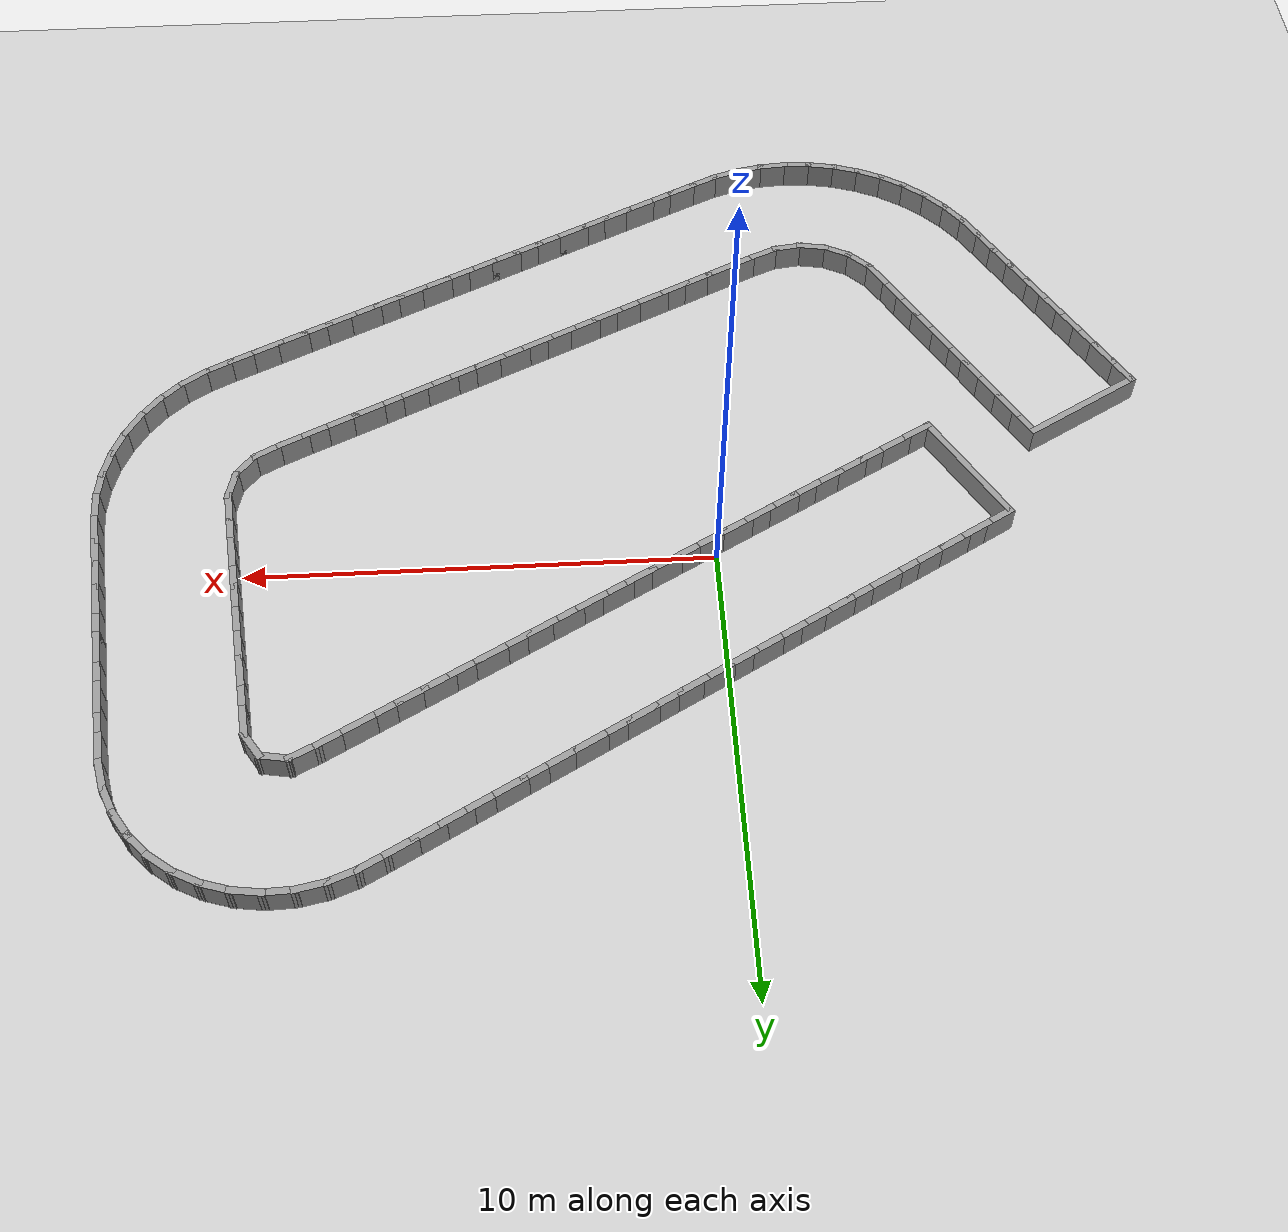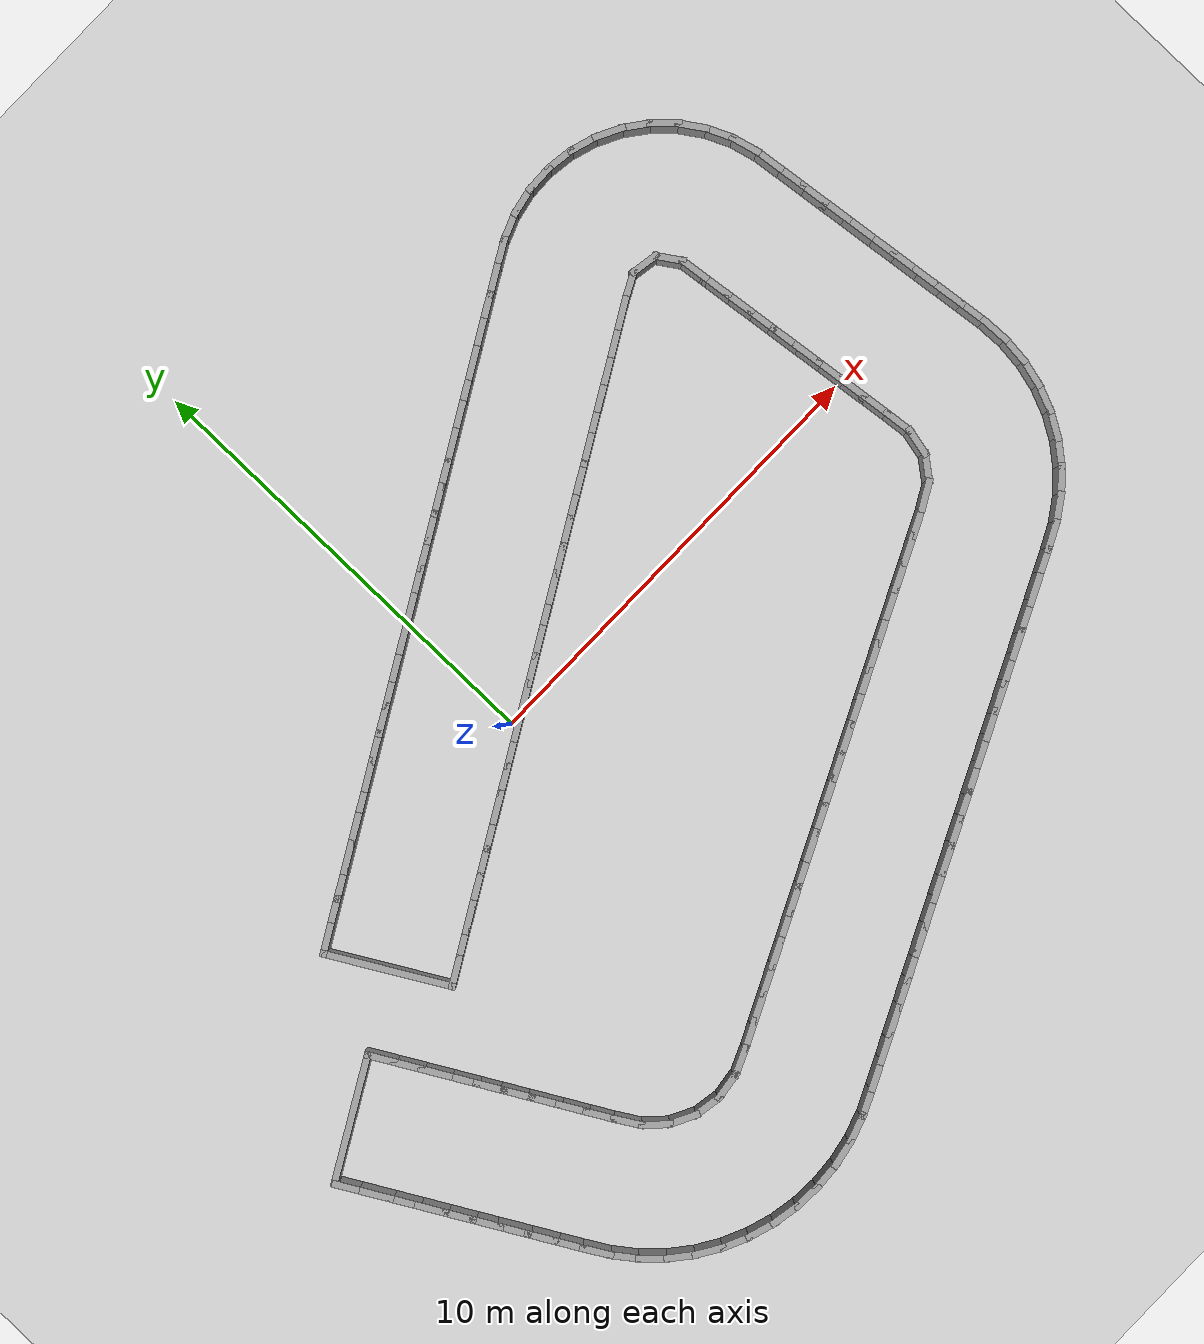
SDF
<?xml version="1.0" ?>
<sdf version='1.7'>
  <world name='default'>
    <plugin name='gazebo_ros_state' filename='libgazebo_ros_state.so'>
      <ros>
        <namespace>/</namespace>
      </ros>
      <update_rate>1000.0</update_rate>
    </plugin>

    <light name='sun' type='directional'>
      <cast_shadows>1</cast_shadows>
      <pose>0 0 10 0 -0 0</pose>
      <diffuse>0.8 0.8 0.8 1</diffuse>
      <specular>0.2 0.2 0.2 1</specular>
      <attenuation>
        <range>1000</range>
        <constant>0.9</constant>
        <linear>0.01</linear>
        <quadratic>0.001</quadratic>
      </attenuation>
      <direction>-0.5 0.1 -0.9</direction>
      <spot>
        <inner_angle>0</inner_angle>
        <outer_angle>0</outer_angle>
        <falloff>0</falloff>
      </spot>
    </light>
    <model name='ground_plane'>
      <static>1</static>
      <link name='link'>
        <collision name='collision'>
          <geometry>
            <plane>
              <normal>0 0 1</normal>
              <size>100 100</size>
            </plane>
          </geometry>
          <surface>
            <friction>
              <ode>
                <mu>100</mu>
                <mu2>50</mu2>
              </ode>
              <torsional>
                <ode/>
              </torsional>
            </friction>
            <contact>
              <ode/>
            </contact>
            <bounce/>
          </surface>
          <max_contacts>10</max_contacts>
        </collision>
        <visual name='visual'>
          <cast_shadows>0</cast_shadows>
          <geometry>
            <plane>
              <normal>0 0 1</normal>
              <size>100 100</size>
            </plane>
          </geometry>
          <material>
            <script>
              <uri>file://media/materials/scripts/gazebo.material</uri>
              <name>Gazebo/Grey</name>
            </script>
          </material>
        </visual>
        <self_collide>0</self_collide>
        <enable_wind>0</enable_wind>
        <kinematic>0</kinematic>
      </link>
    </model>
    <gravity>0 0 -9.8</gravity>
    <magnetic_field>6e-06 2.3e-05 -4.2e-05</magnetic_field>
    <atmosphere type='adiabatic'/>
    <physics type='ode'>
      <max_step_size>0.001</max_step_size>
      <real_time_factor>1</real_time_factor>
      <real_time_update_rate>1000</real_time_update_rate>
    </physics>
    <scene>
      <ambient>0.4 0.4 0.4 1</ambient>
      <background>0.7 0.7 0.7 1</background>
      <shadows>1</shadows>
    </scene>
    <audio>
      <device>default</device>
    </audio>
    <wind/>
    <spherical_coordinates>
      <surface_model>EARTH_WGS84</surface_model>
      <latitude_deg>0</latitude_deg>
      <longitude_deg>0</longitude_deg>
      <elevation>0</elevation>
      <heading_deg>0</heading_deg>
    </spherical_coordinates>
  <model name='rand_turn_11'>
    <pose>0 0 0 0 -0 0</pose>
    <link name='Wall_0'>
      <collision name='Wall_0_Collision'>
        <geometry><box><size>0.7500 0.1500 0.6000</size></box></geometry>
        <pose>0 0 0.3000 0 -0 0</pose>
      </collision>
      <visual name='Wall_0_Visual'>
        <pose>0 0 0.3000 0 -0 0</pose>
        <geometry><box><size>0.7500 0.1500 0.6000</size></box></geometry>
        <material>
          <script>
            <uri>file://media/materials/scripts/gazebo.material</uri>
            <name>Gazebo/Grey</name>
          </script>
          <ambient>1 1 1 1</ambient>
        </material>
      </visual>
      <pose>-5.9878 -0.3365 0 0 -0 0.51695</pose>
    </link>
    <link name='Wall_1'>
      <collision name='Wall_1_Collision'>
        <geometry><box><size>0.7500 0.1500 0.6000</size></box></geometry>
        <pose>0 0 0.3000 0 -0 0</pose>
      </collision>
      <visual name='Wall_1_Visual'>
        <pose>0 0 0.3000 0 -0 0</pose>
        <geometry><box><size>0.7500 0.1500 0.6000</size></box></geometry>
        <material>
          <script>
            <uri>file://media/materials/scripts/gazebo.material</uri>
            <name>Gazebo/Grey</name>
          </script>
          <ambient>1 1 1 1</ambient>
        </material>
      </visual>
      <pose>-5.4662 -0.0400 0 0 -0 0.51695</pose>
    </link>
    <link name='Wall_2'>
      <collision name='Wall_2_Collision'>
        <geometry><box><size>0.7500 0.1500 0.6000</size></box></geometry>
        <pose>0 0 0.3000 0 -0 0</pose>
      </collision>
      <visual name='Wall_2_Visual'>
        <pose>0 0 0.3000 0 -0 0</pose>
        <geometry><box><size>0.7500 0.1500 0.6000</size></box></geometry>
        <material>
          <script>
            <uri>file://media/materials/scripts/gazebo.material</uri>
            <name>Gazebo/Grey</name>
          </script>
          <ambient>1 1 1 1</ambient>
        </material>
      </visual>
      <pose>-4.9446 0.2566 0 0 -0 0.51695</pose>
    </link>
    <link name='Wall_3'>
      <collision name='Wall_3_Collision'>
        <geometry><box><size>0.7500 0.1500 0.6000</size></box></geometry>
        <pose>0 0 0.3000 0 -0 0</pose>
      </collision>
      <visual name='Wall_3_Visual'>
        <pose>0 0 0.3000 0 -0 0</pose>
        <geometry><box><size>0.7500 0.1500 0.6000</size></box></geometry>
        <material>
          <script>
            <uri>file://media/materials/scripts/gazebo.material</uri>
            <name>Gazebo/Grey</name>
          </script>
          <ambient>1 1 1 1</ambient>
        </material>
      </visual>
      <pose>-4.4230 0.5531 0 0 -0 0.51695</pose>
    </link>
    <link name='Wall_4'>
      <collision name='Wall_4_Collision'>
        <geometry><box><size>0.7500 0.1500 0.6000</size></box></geometry>
        <pose>0 0 0.3000 0 -0 0</pose>
      </collision>
      <visual name='Wall_4_Visual'>
        <pose>0 0 0.3000 0 -0 0</pose>
        <geometry><box><size>0.7500 0.1500 0.6000</size></box></geometry>
        <material>
          <script>
            <uri>file://media/materials/scripts/gazebo.material</uri>
            <name>Gazebo/Grey</name>
          </script>
          <ambient>1 1 1 1</ambient>
        </material>
      </visual>
      <pose>-3.9014 0.8496 0 0 -0 0.51695</pose>
    </link>
    <link name='Wall_5'>
      <collision name='Wall_5_Collision'>
        <geometry><box><size>0.7500 0.1500 0.6000</size></box></geometry>
        <pose>0 0 0.3000 0 -0 0</pose>
      </collision>
      <visual name='Wall_5_Visual'>
        <pose>0 0 0.3000 0 -0 0</pose>
        <geometry><box><size>0.7500 0.1500 0.6000</size></box></geometry>
        <material>
          <script>
            <uri>file://media/materials/scripts/gazebo.material</uri>
            <name>Gazebo/Grey</name>
          </script>
          <ambient>1 1 1 1</ambient>
        </material>
      </visual>
      <pose>-3.3798 1.1462 0 0 -0 0.51695</pose>
    </link>
    <link name='Wall_6'>
      <collision name='Wall_6_Collision'>
        <geometry><box><size>0.7500 0.1500 0.6000</size></box></geometry>
        <pose>0 0 0.3000 0 -0 0</pose>
      </collision>
      <visual name='Wall_6_Visual'>
        <pose>0 0 0.3000 0 -0 0</pose>
        <geometry><box><size>0.7500 0.1500 0.6000</size></box></geometry>
        <material>
          <script>
            <uri>file://media/materials/scripts/gazebo.material</uri>
            <name>Gazebo/Grey</name>
          </script>
          <ambient>1 1 1 1</ambient>
        </material>
      </visual>
      <pose>-2.8582 1.4427 0 0 -0 0.51695</pose>
    </link>
    <link name='Wall_7'>
      <collision name='Wall_7_Collision'>
        <geometry><box><size>0.7500 0.1500 0.6000</size></box></geometry>
        <pose>0 0 0.3000 0 -0 0</pose>
      </collision>
      <visual name='Wall_7_Visual'>
        <pose>0 0 0.3000 0 -0 0</pose>
        <geometry><box><size>0.7500 0.1500 0.6000</size></box></geometry>
        <material>
          <script>
            <uri>file://media/materials/scripts/gazebo.material</uri>
            <name>Gazebo/Grey</name>
          </script>
          <ambient>1 1 1 1</ambient>
        </material>
      </visual>
      <pose>-2.3366 1.7393 0 0 -0 0.51695</pose>
    </link>
    <link name='Wall_8'>
      <collision name='Wall_8_Collision'>
        <geometry><box><size>0.7500 0.1500 0.6000</size></box></geometry>
        <pose>0 0 0.3000 0 -0 0</pose>
      </collision>
      <visual name='Wall_8_Visual'>
        <pose>0 0 0.3000 0 -0 0</pose>
        <geometry><box><size>0.7500 0.1500 0.6000</size></box></geometry>
        <material>
          <script>
            <uri>file://media/materials/scripts/gazebo.material</uri>
            <name>Gazebo/Grey</name>
          </script>
          <ambient>1 1 1 1</ambient>
        </material>
      </visual>
      <pose>-1.8150 2.0358 0 0 -0 0.51695</pose>
    </link>
    <link name='Wall_9'>
      <collision name='Wall_9_Collision'>
        <geometry><box><size>0.7500 0.1500 0.6000</size></box></geometry>
        <pose>0 0 0.3000 0 -0 0</pose>
      </collision>
      <visual name='Wall_9_Visual'>
        <pose>0 0 0.3000 0 -0 0</pose>
        <geometry><box><size>0.7500 0.1500 0.6000</size></box></geometry>
        <material>
          <script>
            <uri>file://media/materials/scripts/gazebo.material</uri>
            <name>Gazebo/Grey</name>
          </script>
          <ambient>1 1 1 1</ambient>
        </material>
      </visual>
      <pose>-1.2934 2.3323 0 0 -0 0.51695</pose>
    </link>
    <link name='Wall_10'>
      <collision name='Wall_10_Collision'>
        <geometry><box><size>0.7500 0.1500 0.6000</size></box></geometry>
        <pose>0 0 0.3000 0 -0 0</pose>
      </collision>
      <visual name='Wall_10_Visual'>
        <pose>0 0 0.3000 0 -0 0</pose>
        <geometry><box><size>0.7500 0.1500 0.6000</size></box></geometry>
        <material>
          <script>
            <uri>file://media/materials/scripts/gazebo.material</uri>
            <name>Gazebo/Grey</name>
          </script>
          <ambient>1 1 1 1</ambient>
        </material>
      </visual>
      <pose>-0.7718 2.6289 0 0 -0 0.51695</pose>
    </link>
    <link name='Wall_11'>
      <collision name='Wall_11_Collision'>
        <geometry><box><size>0.7500 0.1500 0.6000</size></box></geometry>
        <pose>0 0 0.3000 0 -0 0</pose>
      </collision>
      <visual name='Wall_11_Visual'>
        <pose>0 0 0.3000 0 -0 0</pose>
        <geometry><box><size>0.7500 0.1500 0.6000</size></box></geometry>
        <material>
          <script>
            <uri>file://media/materials/scripts/gazebo.material</uri>
            <name>Gazebo/Grey</name>
          </script>
          <ambient>1 1 1 1</ambient>
        </material>
      </visual>
      <pose>-0.2502 2.9254 0 0 -0 0.51695</pose>
    </link>
    <link name='Wall_12'>
      <collision name='Wall_12_Collision'>
        <geometry><box><size>0.7500 0.1500 0.6000</size></box></geometry>
        <pose>0 0 0.3000 0 -0 0</pose>
      </collision>
      <visual name='Wall_12_Visual'>
        <pose>0 0 0.3000 0 -0 0</pose>
        <geometry><box><size>0.7500 0.1500 0.6000</size></box></geometry>
        <material>
          <script>
            <uri>file://media/materials/scripts/gazebo.material</uri>
            <name>Gazebo/Grey</name>
          </script>
          <ambient>1 1 1 1</ambient>
        </material>
      </visual>
      <pose>0.2714 3.2220 0 0 -0 0.51695</pose>
    </link>
    <link name='Wall_13'>
      <collision name='Wall_13_Collision'>
        <geometry><box><size>0.7500 0.1500 0.6000</size></box></geometry>
        <pose>0 0 0.3000 0 -0 0</pose>
      </collision>
      <visual name='Wall_13_Visual'>
        <pose>0 0 0.3000 0 -0 0</pose>
        <geometry><box><size>0.7500 0.1500 0.6000</size></box></geometry>
        <material>
          <script>
            <uri>file://media/materials/scripts/gazebo.material</uri>
            <name>Gazebo/Grey</name>
          </script>
          <ambient>1 1 1 1</ambient>
        </material>
      </visual>
      <pose>0.7930 3.5185 0 0 -0 0.51695</pose>
    </link>
    <link name='Wall_14'>
      <collision name='Wall_14_Collision'>
        <geometry><box><size>0.7500 0.1500 0.6000</size></box></geometry>
        <pose>0 0 0.3000 0 -0 0</pose>
      </collision>
      <visual name='Wall_14_Visual'>
        <pose>0 0 0.3000 0 -0 0</pose>
        <geometry><box><size>0.7500 0.1500 0.6000</size></box></geometry>
        <material>
          <script>
            <uri>file://media/materials/scripts/gazebo.material</uri>
            <name>Gazebo/Grey</name>
          </script>
          <ambient>1 1 1 1</ambient>
        </material>
      </visual>
      <pose>1.3146 3.8150 0 0 -0 0.51695</pose>
    </link>
    <link name='Wall_15'>
      <collision name='Wall_15_Collision'>
        <geometry><box><size>0.7500 0.1500 0.6000</size></box></geometry>
        <pose>0 0 0.3000 0 -0 0</pose>
      </collision>
      <visual name='Wall_15_Visual'>
        <pose>0 0 0.3000 0 -0 0</pose>
        <geometry><box><size>0.7500 0.1500 0.6000</size></box></geometry>
        <material>
          <script>
            <uri>file://media/materials/scripts/gazebo.material</uri>
            <name>Gazebo/Grey</name>
          </script>
          <ambient>1 1 1 1</ambient>
        </material>
      </visual>
      <pose>1.8362 4.1116 0 0 -0 0.51695</pose>
    </link>
    <link name='Wall_16'>
      <collision name='Wall_16_Collision'>
        <geometry><box><size>0.7500 0.1500 0.6000</size></box></geometry>
        <pose>0 0 0.3000 0 -0 0</pose>
      </collision>
      <visual name='Wall_16_Visual'>
        <pose>0 0 0.3000 0 -0 0</pose>
        <geometry><box><size>0.7500 0.1500 0.6000</size></box></geometry>
        <material>
          <script>
            <uri>file://media/materials/scripts/gazebo.material</uri>
            <name>Gazebo/Grey</name>
          </script>
          <ambient>1 1 1 1</ambient>
        </material>
      </visual>
      <pose>2.3578 4.4081 0 0 -0 0.51695</pose>
    </link>
    <link name='Wall_17'>
      <collision name='Wall_17_Collision'>
        <geometry><box><size>0.7500 0.1500 0.6000</size></box></geometry>
        <pose>0 0 0.3000 0 -0 0</pose>
      </collision>
      <visual name='Wall_17_Visual'>
        <pose>0 0 0.3000 0 -0 0</pose>
        <geometry><box><size>0.7500 0.1500 0.6000</size></box></geometry>
        <material>
          <script>
            <uri>file://media/materials/scripts/gazebo.material</uri>
            <name>Gazebo/Grey</name>
          </script>
          <ambient>1 1 1 1</ambient>
        </material>
      </visual>
      <pose>2.8794 4.7047 0 0 -0 0.51695</pose>
    </link>
    <link name='Wall_18'>
      <collision name='Wall_18_Collision'>
        <geometry><box><size>0.7500 0.1500 0.6000</size></box></geometry>
        <pose>0 0 0.3000 0 -0 0</pose>
      </collision>
      <visual name='Wall_18_Visual'>
        <pose>0 0 0.3000 0 -0 0</pose>
        <geometry><box><size>0.7500 0.1500 0.6000</size></box></geometry>
        <material>
          <script>
            <uri>file://media/materials/scripts/gazebo.material</uri>
            <name>Gazebo/Grey</name>
          </script>
          <ambient>1 1 1 1</ambient>
        </material>
      </visual>
      <pose>3.4010 5.0012 0 0 -0 0.51695</pose>
    </link>
    <link name='Wall_19'>
      <collision name='Wall_19_Collision'>
        <geometry><box><size>0.7500 0.1500 0.6000</size></box></geometry>
        <pose>0 0 0.3000 0 -0 0</pose>
      </collision>
      <visual name='Wall_19_Visual'>
        <pose>0 0 0.3000 0 -0 0</pose>
        <geometry><box><size>0.7500 0.1500 0.6000</size></box></geometry>
        <material>
          <script>
            <uri>file://media/materials/scripts/gazebo.material</uri>
            <name>Gazebo/Grey</name>
          </script>
          <ambient>1 1 1 1</ambient>
        </material>
      </visual>
      <pose>3.9226 5.2977 0 0 -0 0.51695</pose>
    </link>
    <link name='Wall_20'>
      <collision name='Wall_20_Collision'>
        <geometry><box><size>0.7500 0.1500 0.6000</size></box></geometry>
        <pose>0 0 0.3000 0 -0 0</pose>
      </collision>
      <visual name='Wall_20_Visual'>
        <pose>0 0 0.3000 0 -0 0</pose>
        <geometry><box><size>0.7500 0.1500 0.6000</size></box></geometry>
        <material>
          <script>
            <uri>file://media/materials/scripts/gazebo.material</uri>
            <name>Gazebo/Grey</name>
          </script>
          <ambient>1 1 1 1</ambient>
        </material>
      </visual>
      <pose>4.4442 5.5943 0 0 -0 0.51695</pose>
    </link>
    <link name='Wall_21'>
      <collision name='Wall_21_Collision'>
        <geometry><box><size>0.7500 0.1500 0.6000</size></box></geometry>
        <pose>0 0 0.3000 0 -0 0</pose>
      </collision>
      <visual name='Wall_21_Visual'>
        <pose>0 0 0.3000 0 -0 0</pose>
        <geometry><box><size>0.7500 0.1500 0.6000</size></box></geometry>
        <material>
          <script>
            <uri>file://media/materials/scripts/gazebo.material</uri>
            <name>Gazebo/Grey</name>
          </script>
          <ambient>1 1 1 1</ambient>
        </material>
      </visual>
      <pose>4.9658 5.8908 0 0 -0 0.51695</pose>
    </link>
    <link name='Wall_22'>
      <collision name='Wall_22_Collision'>
        <geometry><box><size>0.7500 0.1500 0.6000</size></box></geometry>
        <pose>0 0 0.3000 0 -0 0</pose>
      </collision>
      <visual name='Wall_22_Visual'>
        <pose>0 0 0.3000 0 -0 0</pose>
        <geometry><box><size>0.7500 0.1500 0.6000</size></box></geometry>
        <material>
          <script>
            <uri>file://media/materials/scripts/gazebo.material</uri>
            <name>Gazebo/Grey</name>
          </script>
          <ambient>1 1 1 1</ambient>
        </material>
      </visual>
      <pose>5.4874 6.1874 0 0 -0 0.51695</pose>
    </link>
    <link name='Wall_23'>
      <collision name='Wall_23_Collision'>
        <geometry><box><size>0.7500 0.1500 0.6000</size></box></geometry>
        <pose>0 0 0.3000 0 -0 0</pose>
      </collision>
      <visual name='Wall_23_Visual'>
        <pose>0 0 0.3000 0 -0 0</pose>
        <geometry><box><size>0.7500 0.1500 0.6000</size></box></geometry>
        <material>
          <script>
            <uri>file://media/materials/scripts/gazebo.material</uri>
            <name>Gazebo/Grey</name>
          </script>
          <ambient>1 1 1 1</ambient>
        </material>
      </visual>
      <pose>6.0089 6.4839 0 0 -0 0.51695</pose>
    </link>
    <link name='Wall_24'>
      <collision name='Wall_24_Collision'>
        <geometry><box><size>0.7500 0.1500 0.6000</size></box></geometry>
        <pose>0 0 0.3000 0 -0 0</pose>
      </collision>
      <visual name='Wall_24_Visual'>
        <pose>0 0 0.3000 0 -0 0</pose>
        <geometry><box><size>0.7500 0.1500 0.6000</size></box></geometry>
        <material>
          <script>
            <uri>file://media/materials/scripts/gazebo.material</uri>
            <name>Gazebo/Grey</name>
          </script>
          <ambient>1 1 1 1</ambient>
        </material>
      </visual>
      <pose>6.5305 6.7805 0 0 -0 0.51695</pose>
    </link>
    <link name='Wall_25'>
      <collision name='Wall_25_Collision'>
        <geometry><box><size>0.7499 0.1500 0.6000</size></box></geometry>
        <pose>0 0 0.3000 0 -0 0</pose>
      </collision>
      <visual name='Wall_25_Visual'>
        <pose>0 0 0.3000 0 -0 0</pose>
        <geometry><box><size>0.7499 0.1500 0.6000</size></box></geometry>
        <material>
          <script>
            <uri>file://media/materials/scripts/gazebo.material</uri>
            <name>Gazebo/Grey</name>
          </script>
          <ambient>1 1 1 1</ambient>
        </material>
      </visual>
      <pose>7.0536 7.0742 0 0 -0 0.50648</pose>
    </link>
    <link name='Wall_26'>
      <collision name='Wall_26_Collision'>
        <geometry><box><size>0.7492 0.1500 0.6000</size></box></geometry>
        <pose>0 0 0.3000 0 -0 0</pose>
      </collision>
      <visual name='Wall_26_Visual'>
        <pose>0 0 0.3000 0 -0 0</pose>
        <geometry><box><size>0.7492 0.1500 0.6000</size></box></geometry>
        <material>
          <script>
            <uri>file://media/materials/scripts/gazebo.material</uri>
            <name>Gazebo/Grey</name>
          </script>
          <ambient>1 1 1 1</ambient>
        </material>
      </visual>
      <pose>7.5946 7.3297 0 0 -0 0.37580</pose>
    </link>
    <link name='Wall_27'>
      <collision name='Wall_27_Collision'>
        <geometry><box><size>0.7492 0.1500 0.6000</size></box></geometry>
        <pose>0 0 0.3000 0 -0 0</pose>
      </collision>
      <visual name='Wall_27_Visual'>
        <pose>0 0 0.3000 0 -0 0</pose>
        <geometry><box><size>0.7492 0.1500 0.6000</size></box></geometry>
        <material>
          <script>
            <uri>file://media/materials/scripts/gazebo.material</uri>
            <name>Gazebo/Grey</name>
          </script>
          <ambient>1 1 1 1</ambient>
        </material>
      </visual>
      <pose>8.1667 7.5008 0 0 -0 0.20546</pose>
    </link>
    <link name='Wall_28'>
      <collision name='Wall_28_Collision'>
        <geometry><box><size>0.7492 0.1500 0.6000</size></box></geometry>
        <pose>0 0 0.3000 0 -0 0</pose>
      </collision>
      <visual name='Wall_28_Visual'>
        <pose>0 0 0.3000 0 -0 0</pose>
        <geometry><box><size>0.7492 0.1500 0.6000</size></box></geometry>
        <material>
          <script>
            <uri>file://media/materials/scripts/gazebo.material</uri>
            <name>Gazebo/Grey</name>
          </script>
          <ambient>1 1 1 1</ambient>
        </material>
      </visual>
      <pose>8.7594 7.5732 0 0 -0 0.03778</pose>
    </link>
    <link name='Wall_29'>
      <collision name='Wall_29_Collision'>
        <geometry><box><size>0.7493 0.1500 0.6000</size></box></geometry>
        <pose>0 0 0.3000 0 -0 0</pose>
      </collision>
      <visual name='Wall_29_Visual'>
        <pose>0 0 0.3000 0 -0 0</pose>
        <geometry><box><size>0.7493 0.1500 0.6000</size></box></geometry>
        <material>
          <script>
            <uri>file://media/materials/scripts/gazebo.material</uri>
            <name>Gazebo/Grey</name>
          </script>
          <ambient>1 1 1 1</ambient>
        </material>
      </visual>
      <pose>9.3557 7.5445 0 0 -0 -0.13394</pose>
    </link>
    <link name='Wall_30'>
      <collision name='Wall_30_Collision'>
        <geometry><box><size>0.7492 0.1500 0.6000</size></box></geometry>
        <pose>0 0 0.3000 0 -0 0</pose>
      </collision>
      <visual name='Wall_30_Visual'>
        <pose>0 0 0.3000 0 -0 0</pose>
        <geometry><box><size>0.7492 0.1500 0.6000</size></box></geometry>
        <material>
          <script>
            <uri>file://media/materials/scripts/gazebo.material</uri>
            <name>Gazebo/Grey</name>
          </script>
          <ambient>1 1 1 1</ambient>
        </material>
      </visual>
      <pose>9.9386 7.4153 0 0 -0 -0.30248</pose>
    </link>
    <link name='Wall_31'>
      <collision name='Wall_31_Collision'>
        <geometry><box><size>0.7493 0.1500 0.6000</size></box></geometry>
        <pose>0 0 0.3000 0 -0 0</pose>
      </collision>
      <visual name='Wall_31_Visual'>
        <pose>0 0 0.3000 0 -0 0</pose>
        <geometry><box><size>0.7493 0.1500 0.6000</size></box></geometry>
        <material>
          <script>
            <uri>file://media/materials/scripts/gazebo.material</uri>
            <name>Gazebo/Grey</name>
          </script>
          <ambient>1 1 1 1</ambient>
        </material>
      </visual>
      <pose>10.4916 7.1900 0 0 -0 -0.47110</pose>
    </link>
    <link name='Wall_32'>
      <collision name='Wall_32_Collision'>
        <geometry><box><size>0.7492 0.1500 0.6000</size></box></geometry>
        <pose>0 0 0.3000 0 -0 0</pose>
      </collision>
      <visual name='Wall_32_Visual'>
        <pose>0 0 0.3000 0 -0 0</pose>
        <geometry><box><size>0.7492 0.1500 0.6000</size></box></geometry>
        <material>
          <script>
            <uri>file://media/materials/scripts/gazebo.material</uri>
            <name>Gazebo/Grey</name>
          </script>
          <ambient>1 1 1 1</ambient>
        </material>
      </visual>
      <pose>10.9984 6.8745 0 0 -0 -0.64274</pose>
    </link>
    <link name='Wall_33'>
      <collision name='Wall_33_Collision'>
        <geometry><box><size>0.7492 0.1500 0.6000</size></box></geometry>
        <pose>0 0 0.3000 0 -0 0</pose>
      </collision>
      <visual name='Wall_33_Visual'>
        <pose>0 0 0.3000 0 -0 0</pose>
        <geometry><box><size>0.7492 0.1500 0.6000</size></box></geometry>
        <material>
          <script>
            <uri>file://media/materials/scripts/gazebo.material</uri>
            <name>Gazebo/Grey</name>
          </script>
          <ambient>1 1 1 1</ambient>
        </material>
      </visual>
      <pose>11.4448 6.4778 0 0 -0 -0.81042</pose>
    </link>
    <link name='Wall_34'>
      <collision name='Wall_34_Collision'>
        <geometry><box><size>0.7492 0.1500 0.6000</size></box></geometry>
        <pose>0 0 0.3000 0 -0 0</pose>
      </collision>
      <visual name='Wall_34_Visual'>
        <pose>0 0 0.3000 0 -0 0</pose>
        <geometry><box><size>0.7492 0.1500 0.6000</size></box></geometry>
        <material>
          <script>
            <uri>file://media/materials/scripts/gazebo.material</uri>
            <name>Gazebo/Grey</name>
          </script>
          <ambient>1 1 1 1</ambient>
        </material>
      </visual>
      <pose>11.8179 6.0117 0 0 -0 -0.98085</pose>
    </link>
    <link name='Wall_35'>
      <collision name='Wall_35_Collision'>
        <geometry><box><size>0.7492 0.1500 0.6000</size></box></geometry>
        <pose>0 0 0.3000 0 -0 0</pose>
      </collision>
      <visual name='Wall_35_Visual'>
        <pose>0 0 0.3000 0 -0 0</pose>
        <geometry><box><size>0.7492 0.1500 0.6000</size></box></geometry>
        <material>
          <script>
            <uri>file://media/materials/scripts/gazebo.material</uri>
            <name>Gazebo/Grey</name>
          </script>
          <ambient>1 1 1 1</ambient>
        </material>
      </visual>
      <pose>12.1068 5.4892 0 0 -0 -1.15068</pose>
    </link>
    <link name='Wall_36'>
      <collision name='Wall_36_Collision'>
        <geometry><box><size>0.7492 0.1500 0.6000</size></box></geometry>
        <pose>0 0 0.3000 0 -0 0</pose>
      </collision>
      <visual name='Wall_36_Visual'>
        <pose>0 0 0.3000 0 -0 0</pose>
        <geometry><box><size>0.7492 0.1500 0.6000</size></box></geometry>
        <material>
          <script>
            <uri>file://media/materials/scripts/gazebo.material</uri>
            <name>Gazebo/Grey</name>
          </script>
          <ambient>1 1 1 1</ambient>
        </material>
      </visual>
      <pose>12.3037 4.9255 0 0 -0 -1.31870</pose>
    </link>
    <link name='Wall_37'>
      <collision name='Wall_37_Collision'>
        <geometry><box><size>0.7500 0.1500 0.6000</size></box></geometry>
        <pose>0 0 0.3000 0 -0 0</pose>
      </collision>
      <visual name='Wall_37_Visual'>
        <pose>0 0 0.3000 0 -0 0</pose>
        <geometry><box><size>0.7500 0.1500 0.6000</size></box></geometry>
        <material>
          <script>
            <uri>file://media/materials/scripts/gazebo.material</uri>
            <name>Gazebo/Grey</name>
          </script>
          <ambient>1 1 1 1</ambient>
        </material>
      </visual>
      <pose>12.4158 4.3377 0 0 -0 -1.44592</pose>
    </link>
    <link name='Wall_38'>
      <collision name='Wall_38_Collision'>
        <geometry><box><size>0.7500 0.1500 0.6000</size></box></geometry>
        <pose>0 0 0.3000 0 -0 0</pose>
      </collision>
      <visual name='Wall_38_Visual'>
        <pose>0 0 0.3000 0 -0 0</pose>
        <geometry><box><size>0.7500 0.1500 0.6000</size></box></geometry>
        <material>
          <script>
            <uri>file://media/materials/scripts/gazebo.material</uri>
            <name>Gazebo/Grey</name>
          </script>
          <ambient>1 1 1 1</ambient>
        </material>
      </visual>
      <pose>12.4898 3.7423 0 0 -0 -1.44849</pose>
    </link>
    <link name='Wall_39'>
      <collision name='Wall_39_Collision'>
        <geometry><box><size>0.7500 0.1500 0.6000</size></box></geometry>
        <pose>0 0 0.3000 0 -0 0</pose>
      </collision>
      <visual name='Wall_39_Visual'>
        <pose>0 0 0.3000 0 -0 0</pose>
        <geometry><box><size>0.7500 0.1500 0.6000</size></box></geometry>
        <material>
          <script>
            <uri>file://media/materials/scripts/gazebo.material</uri>
            <name>Gazebo/Grey</name>
          </script>
          <ambient>1 1 1 1</ambient>
        </material>
      </visual>
      <pose>12.5630 3.1468 0 0 -0 -1.44849</pose>
    </link>
    <link name='Wall_40'>
      <collision name='Wall_40_Collision'>
        <geometry><box><size>0.7500 0.1500 0.6000</size></box></geometry>
        <pose>0 0 0.3000 0 -0 0</pose>
      </collision>
      <visual name='Wall_40_Visual'>
        <pose>0 0 0.3000 0 -0 0</pose>
        <geometry><box><size>0.7500 0.1500 0.6000</size></box></geometry>
        <material>
          <script>
            <uri>file://media/materials/scripts/gazebo.material</uri>
            <name>Gazebo/Grey</name>
          </script>
          <ambient>1 1 1 1</ambient>
        </material>
      </visual>
      <pose>12.6362 2.5513 0 0 -0 -1.44849</pose>
    </link>
    <link name='Wall_41'>
      <collision name='Wall_41_Collision'>
        <geometry><box><size>0.7500 0.1500 0.6000</size></box></geometry>
        <pose>0 0 0.3000 0 -0 0</pose>
      </collision>
      <visual name='Wall_41_Visual'>
        <pose>0 0 0.3000 0 -0 0</pose>
        <geometry><box><size>0.7500 0.1500 0.6000</size></box></geometry>
        <material>
          <script>
            <uri>file://media/materials/scripts/gazebo.material</uri>
            <name>Gazebo/Grey</name>
          </script>
          <ambient>1 1 1 1</ambient>
        </material>
      </visual>
      <pose>12.7094 1.9557 0 0 -0 -1.44849</pose>
    </link>
    <link name='Wall_42'>
      <collision name='Wall_42_Collision'>
        <geometry><box><size>0.7500 0.1500 0.6000</size></box></geometry>
        <pose>0 0 0.3000 0 -0 0</pose>
      </collision>
      <visual name='Wall_42_Visual'>
        <pose>0 0 0.3000 0 -0 0</pose>
        <geometry><box><size>0.7500 0.1500 0.6000</size></box></geometry>
        <material>
          <script>
            <uri>file://media/materials/scripts/gazebo.material</uri>
            <name>Gazebo/Grey</name>
          </script>
          <ambient>1 1 1 1</ambient>
        </material>
      </visual>
      <pose>12.7826 1.3602 0 0 -0 -1.44849</pose>
    </link>
    <link name='Wall_43'>
      <collision name='Wall_43_Collision'>
        <geometry><box><size>0.7500 0.1500 0.6000</size></box></geometry>
        <pose>0 0 0.3000 0 -0 0</pose>
      </collision>
      <visual name='Wall_43_Visual'>
        <pose>0 0 0.3000 0 -0 0</pose>
        <geometry><box><size>0.7500 0.1500 0.6000</size></box></geometry>
        <material>
          <script>
            <uri>file://media/materials/scripts/gazebo.material</uri>
            <name>Gazebo/Grey</name>
          </script>
          <ambient>1 1 1 1</ambient>
        </material>
      </visual>
      <pose>12.8558 0.7647 0 0 -0 -1.44849</pose>
    </link>
    <link name='Wall_44'>
      <collision name='Wall_44_Collision'>
        <geometry><box><size>0.7500 0.1500 0.6000</size></box></geometry>
        <pose>0 0 0.3000 0 -0 0</pose>
      </collision>
      <visual name='Wall_44_Visual'>
        <pose>0 0 0.3000 0 -0 0</pose>
        <geometry><box><size>0.7500 0.1500 0.6000</size></box></geometry>
        <material>
          <script>
            <uri>file://media/materials/scripts/gazebo.material</uri>
            <name>Gazebo/Grey</name>
          </script>
          <ambient>1 1 1 1</ambient>
        </material>
      </visual>
      <pose>12.9290 0.1692 0 0 -0 -1.44849</pose>
    </link>
    <link name='Wall_45'>
      <collision name='Wall_45_Collision'>
        <geometry><box><size>0.7500 0.1500 0.6000</size></box></geometry>
        <pose>0 0 0.3000 0 -0 0</pose>
      </collision>
      <visual name='Wall_45_Visual'>
        <pose>0 0 0.3000 0 -0 0</pose>
        <geometry><box><size>0.7500 0.1500 0.6000</size></box></geometry>
        <material>
          <script>
            <uri>file://media/materials/scripts/gazebo.material</uri>
            <name>Gazebo/Grey</name>
          </script>
          <ambient>1 1 1 1</ambient>
        </material>
      </visual>
      <pose>13.0022 -0.4263 0 0 -0 -1.44849</pose>
    </link>
    <link name='Wall_46'>
      <collision name='Wall_46_Collision'>
        <geometry><box><size>0.7500 0.1500 0.6000</size></box></geometry>
        <pose>0 0 0.3000 0 -0 0</pose>
      </collision>
      <visual name='Wall_46_Visual'>
        <pose>0 0 0.3000 0 -0 0</pose>
        <geometry><box><size>0.7500 0.1500 0.6000</size></box></geometry>
        <material>
          <script>
            <uri>file://media/materials/scripts/gazebo.material</uri>
            <name>Gazebo/Grey</name>
          </script>
          <ambient>1 1 1 1</ambient>
        </material>
      </visual>
      <pose>13.0751 -1.0219 0 0 -0 -1.44950</pose>
    </link>
    <link name='Wall_47'>
      <collision name='Wall_47_Collision'>
        <geometry><box><size>0.7494 0.1500 0.6000</size></box></geometry>
        <pose>0 0 0.3000 0 -0 0</pose>
      </collision>
      <visual name='Wall_47_Visual'>
        <pose>0 0 0.3000 0 -0 0</pose>
        <geometry><box><size>0.7494 0.1500 0.6000</size></box></geometry>
        <material>
          <script>
            <uri>file://media/materials/scripts/gazebo.material</uri>
            <name>Gazebo/Grey</name>
          </script>
          <ambient>1 1 1 1</ambient>
        </material>
      </visual>
      <pose>13.1234 -1.6192 0 0 -0 -1.53078</pose>
    </link>
    <link name='Wall_48'>
      <collision name='Wall_48_Collision'>
        <geometry><box><size>0.7494 0.1500 0.6000</size></box></geometry>
        <pose>0 0 0.3000 0 -0 0</pose>
      </collision>
      <visual name='Wall_48_Visual'>
        <pose>0 0 0.3000 0 -0 0</pose>
        <geometry><box><size>0.7494 0.1500 0.6000</size></box></geometry>
        <material>
          <script>
            <uri>file://media/materials/scripts/gazebo.material</uri>
            <name>Gazebo/Grey</name>
          </script>
          <ambient>1 1 1 1</ambient>
        </material>
      </visual>
      <pose>13.1042 -2.2167 0 0 -0 -1.67504</pose>
    </link>
    <link name='Wall_49'>
      <collision name='Wall_49_Collision'>
        <geometry><box><size>0.7494 0.1500 0.6000</size></box></geometry>
        <pose>0 0 0.3000 0 -0 0</pose>
      </collision>
      <visual name='Wall_49_Visual'>
        <pose>0 0 0.3000 0 -0 0</pose>
        <geometry><box><size>0.7494 0.1500 0.6000</size></box></geometry>
        <material>
          <script>
            <uri>file://media/materials/scripts/gazebo.material</uri>
            <name>Gazebo/Grey</name>
          </script>
          <ambient>1 1 1 1</ambient>
        </material>
      </visual>
      <pose>12.9992 -2.8053 0 0 -0 -1.81954</pose>
    </link>
    <link name='Wall_50'>
      <collision name='Wall_50_Collision'>
        <geometry><box><size>0.7495 0.1500 0.6000</size></box></geometry>
        <pose>0 0 0.3000 0 -0 0</pose>
      </collision>
      <visual name='Wall_50_Visual'>
        <pose>0 0 0.3000 0 -0 0</pose>
        <geometry><box><size>0.7495 0.1500 0.6000</size></box></geometry>
        <material>
          <script>
            <uri>file://media/materials/scripts/gazebo.material</uri>
            <name>Gazebo/Grey</name>
          </script>
          <ambient>1 1 1 1</ambient>
        </material>
      </visual>
      <pose>12.8106 -3.3727 0 0 -0 -1.96403</pose>
    </link>
    <link name='Wall_51'>
      <collision name='Wall_51_Collision'>
        <geometry><box><size>0.7495 0.1500 0.6000</size></box></geometry>
        <pose>0 0 0.3000 0 -0 0</pose>
      </collision>
      <visual name='Wall_51_Visual'>
        <pose>0 0 0.3000 0 -0 0</pose>
        <geometry><box><size>0.7495 0.1500 0.6000</size></box></geometry>
        <material>
          <script>
            <uri>file://media/materials/scripts/gazebo.material</uri>
            <name>Gazebo/Grey</name>
          </script>
          <ambient>1 1 1 1</ambient>
        </material>
      </visual>
      <pose>12.5422 -3.9070 0 0 -0 -2.10853</pose>
    </link>
    <link name='Wall_52'>
      <collision name='Wall_52_Collision'>
        <geometry><box><size>0.7495 0.1500 0.6000</size></box></geometry>
        <pose>0 0 0.3000 0 -0 0</pose>
      </collision>
      <visual name='Wall_52_Visual'>
        <pose>0 0 0.3000 0 -0 0</pose>
        <geometry><box><size>0.7495 0.1500 0.6000</size></box></geometry>
        <material>
          <script>
            <uri>file://media/materials/scripts/gazebo.material</uri>
            <name>Gazebo/Grey</name>
          </script>
          <ambient>1 1 1 1</ambient>
        </material>
      </visual>
      <pose>12.1997 -4.3970 0 0 -0 -2.25303</pose>
    </link>
    <link name='Wall_53'>
      <collision name='Wall_53_Collision'>
        <geometry><box><size>0.7495 0.1500 0.6000</size></box></geometry>
        <pose>0 0 0.3000 0 -0 0</pose>
      </collision>
      <visual name='Wall_53_Visual'>
        <pose>0 0 0.3000 0 -0 0</pose>
        <geometry><box><size>0.7495 0.1500 0.6000</size></box></geometry>
        <material>
          <script>
            <uri>file://media/materials/scripts/gazebo.material</uri>
            <name>Gazebo/Grey</name>
          </script>
          <ambient>1 1 1 1</ambient>
        </material>
      </visual>
      <pose>11.7902 -4.8327 0 0 -0 -2.39752</pose>
    </link>
    <link name='Wall_54'>
      <collision name='Wall_54_Collision'>
        <geometry><box><size>0.7495 0.1500 0.6000</size></box></geometry>
        <pose>0 0 0.3000 0 -0 0</pose>
      </collision>
      <visual name='Wall_54_Visual'>
        <pose>0 0 0.3000 0 -0 0</pose>
        <geometry><box><size>0.7495 0.1500 0.6000</size></box></geometry>
        <material>
          <script>
            <uri>file://media/materials/scripts/gazebo.material</uri>
            <name>Gazebo/Grey</name>
          </script>
          <ambient>1 1 1 1</ambient>
        </material>
      </visual>
      <pose>11.3222 -5.2048 0 0 -0 -2.54202</pose>
    </link>
    <link name='Wall_55'>
      <collision name='Wall_55_Collision'>
        <geometry><box><size>0.7498 0.1500 0.6000</size></box></geometry>
        <pose>0 0 0.3000 0 -0 0</pose>
      </collision>
      <visual name='Wall_55_Visual'>
        <pose>0 0 0.3000 0 -0 0</pose>
        <geometry><box><size>0.7498 0.1500 0.6000</size></box></geometry>
        <material>
          <script>
            <uri>file://media/materials/scripts/gazebo.material</uri>
            <name>Gazebo/Grey</name>
          </script>
          <ambient>1 1 1 1</ambient>
        </material>
      </visual>
      <pose>10.8072 -5.5096 0 0 -0 -2.67236</pose>
    </link>
    <link name='Wall_56'>
      <collision name='Wall_56_Collision'>
        <geometry><box><size>0.7500 0.1500 0.6000</size></box></geometry>
        <pose>0 0 0.3000 0 -0 0</pose>
      </collision>
      <visual name='Wall_56_Visual'>
        <pose>0 0 0.3000 0 -0 0</pose>
        <geometry><box><size>0.7500 0.1500 0.6000</size></box></geometry>
        <material>
          <script>
            <uri>file://media/materials/scripts/gazebo.material</uri>
            <name>Gazebo/Grey</name>
          </script>
          <ambient>1 1 1 1</ambient>
        </material>
      </visual>
      <pose>10.2692 -5.7749 0 0 -0 -2.69464</pose>
    </link>
    <link name='Wall_57'>
      <collision name='Wall_57_Collision'>
        <geometry><box><size>0.7500 0.1500 0.6000</size></box></geometry>
        <pose>0 0 0.3000 0 -0 0</pose>
      </collision>
      <visual name='Wall_57_Visual'>
        <pose>0 0 0.3000 0 -0 0</pose>
        <geometry><box><size>0.7500 0.1500 0.6000</size></box></geometry>
        <material>
          <script>
            <uri>file://media/materials/scripts/gazebo.material</uri>
            <name>Gazebo/Grey</name>
          </script>
          <ambient>1 1 1 1</ambient>
        </material>
      </visual>
      <pose>9.7282 -6.0342 0 0 -0 -2.69464</pose>
    </link>
    <link name='Wall_58'>
      <collision name='Wall_58_Collision'>
        <geometry><box><size>0.7500 0.1500 0.6000</size></box></geometry>
        <pose>0 0 0.3000 0 -0 0</pose>
      </collision>
      <visual name='Wall_58_Visual'>
        <pose>0 0 0.3000 0 -0 0</pose>
        <geometry><box><size>0.7500 0.1500 0.6000</size></box></geometry>
        <material>
          <script>
            <uri>file://media/materials/scripts/gazebo.material</uri>
            <name>Gazebo/Grey</name>
          </script>
          <ambient>1 1 1 1</ambient>
        </material>
      </visual>
      <pose>9.1871 -6.2935 0 0 -0 -2.69464</pose>
    </link>
    <link name='Wall_59'>
      <collision name='Wall_59_Collision'>
        <geometry><box><size>0.7500 0.1500 0.6000</size></box></geometry>
        <pose>0 0 0.3000 0 -0 0</pose>
      </collision>
      <visual name='Wall_59_Visual'>
        <pose>0 0 0.3000 0 -0 0</pose>
        <geometry><box><size>0.7500 0.1500 0.6000</size></box></geometry>
        <material>
          <script>
            <uri>file://media/materials/scripts/gazebo.material</uri>
            <name>Gazebo/Grey</name>
          </script>
          <ambient>1 1 1 1</ambient>
        </material>
      </visual>
      <pose>8.6460 -6.5529 0 0 -0 -2.69464</pose>
    </link>
    <link name='Wall_60'>
      <collision name='Wall_60_Collision'>
        <geometry><box><size>0.7500 0.1500 0.6000</size></box></geometry>
        <pose>0 0 0.3000 0 -0 0</pose>
      </collision>
      <visual name='Wall_60_Visual'>
        <pose>0 0 0.3000 0 -0 0</pose>
        <geometry><box><size>0.7500 0.1500 0.6000</size></box></geometry>
        <material>
          <script>
            <uri>file://media/materials/scripts/gazebo.material</uri>
            <name>Gazebo/Grey</name>
          </script>
          <ambient>1 1 1 1</ambient>
        </material>
      </visual>
      <pose>8.1050 -6.8122 0 0 -0 -2.69464</pose>
    </link>
    <link name='Wall_61'>
      <collision name='Wall_61_Collision'>
        <geometry><box><size>0.7500 0.1500 0.6000</size></box></geometry>
        <pose>0 0 0.3000 0 -0 0</pose>
      </collision>
      <visual name='Wall_61_Visual'>
        <pose>0 0 0.3000 0 -0 0</pose>
        <geometry><box><size>0.7500 0.1500 0.6000</size></box></geometry>
        <material>
          <script>
            <uri>file://media/materials/scripts/gazebo.material</uri>
            <name>Gazebo/Grey</name>
          </script>
          <ambient>1 1 1 1</ambient>
        </material>
      </visual>
      <pose>7.5639 -7.0715 0 0 -0 -2.69464</pose>
    </link>
    <link name='Wall_62'>
      <collision name='Wall_62_Collision'>
        <geometry><box><size>0.7500 0.1500 0.6000</size></box></geometry>
        <pose>0 0 0.3000 0 -0 0</pose>
      </collision>
      <visual name='Wall_62_Visual'>
        <pose>0 0 0.3000 0 -0 0</pose>
        <geometry><box><size>0.7500 0.1500 0.6000</size></box></geometry>
        <material>
          <script>
            <uri>file://media/materials/scripts/gazebo.material</uri>
            <name>Gazebo/Grey</name>
          </script>
          <ambient>1 1 1 1</ambient>
        </material>
      </visual>
      <pose>7.0229 -7.3309 0 0 -0 -2.69464</pose>
    </link>
    <link name='Wall_63'>
      <collision name='Wall_63_Collision'>
        <geometry><box><size>0.7500 0.1500 0.6000</size></box></geometry>
        <pose>0 0 0.3000 0 -0 0</pose>
      </collision>
      <visual name='Wall_63_Visual'>
        <pose>0 0 0.3000 0 -0 0</pose>
        <geometry><box><size>0.7500 0.1500 0.6000</size></box></geometry>
        <material>
          <script>
            <uri>file://media/materials/scripts/gazebo.material</uri>
            <name>Gazebo/Grey</name>
          </script>
          <ambient>1 1 1 1</ambient>
        </material>
      </visual>
      <pose>6.4818 -7.5902 0 0 -0 -2.69464</pose>
    </link>
    <link name='Wall_64'>
      <collision name='Wall_64_Collision'>
        <geometry><box><size>0.7500 0.1500 0.6000</size></box></geometry>
        <pose>0 0 0.3000 0 -0 0</pose>
      </collision>
      <visual name='Wall_64_Visual'>
        <pose>0 0 0.3000 0 -0 0</pose>
        <geometry><box><size>0.7500 0.1500 0.6000</size></box></geometry>
        <material>
          <script>
            <uri>file://media/materials/scripts/gazebo.material</uri>
            <name>Gazebo/Grey</name>
          </script>
          <ambient>1 1 1 1</ambient>
        </material>
      </visual>
      <pose>5.9407 -7.8495 0 0 -0 -2.69464</pose>
    </link>
    <link name='Wall_65'>
      <collision name='Wall_65_Collision'>
        <geometry><box><size>0.7500 0.1500 0.6000</size></box></geometry>
        <pose>0 0 0.3000 0 -0 0</pose>
      </collision>
      <visual name='Wall_65_Visual'>
        <pose>0 0 0.3000 0 -0 0</pose>
        <geometry><box><size>0.7500 0.1500 0.6000</size></box></geometry>
        <material>
          <script>
            <uri>file://media/materials/scripts/gazebo.material</uri>
            <name>Gazebo/Grey</name>
          </script>
          <ambient>1 1 1 1</ambient>
        </material>
      </visual>
      <pose>5.3997 -8.1089 0 0 -0 -2.69464</pose>
    </link>
    <link name='Wall_66'>
      <collision name='Wall_66_Collision'>
        <geometry><box><size>0.7500 0.1500 0.6000</size></box></geometry>
        <pose>0 0 0.3000 0 -0 0</pose>
      </collision>
      <visual name='Wall_66_Visual'>
        <pose>0 0 0.3000 0 -0 0</pose>
        <geometry><box><size>0.7500 0.1500 0.6000</size></box></geometry>
        <material>
          <script>
            <uri>file://media/materials/scripts/gazebo.material</uri>
            <name>Gazebo/Grey</name>
          </script>
          <ambient>1 1 1 1</ambient>
        </material>
      </visual>
      <pose>4.8586 -8.3682 0 0 -0 -2.69464</pose>
    </link>
    <link name='Wall_67'>
      <collision name='Wall_67_Collision'>
        <geometry><box><size>0.7500 0.1500 0.6000</size></box></geometry>
        <pose>0 0 0.3000 0 -0 0</pose>
      </collision>
      <visual name='Wall_67_Visual'>
        <pose>0 0 0.3000 0 -0 0</pose>
        <geometry><box><size>0.7500 0.1500 0.6000</size></box></geometry>
        <material>
          <script>
            <uri>file://media/materials/scripts/gazebo.material</uri>
            <name>Gazebo/Grey</name>
          </script>
          <ambient>1 1 1 1</ambient>
        </material>
      </visual>
      <pose>4.3176 -8.6275 0 0 -0 -2.69464</pose>
    </link>
    <link name='Wall_68'>
      <collision name='Wall_68_Collision'>
        <geometry><box><size>0.7500 0.1500 0.6000</size></box></geometry>
        <pose>0 0 0.3000 0 -0 0</pose>
      </collision>
      <visual name='Wall_68_Visual'>
        <pose>0 0 0.3000 0 -0 0</pose>
        <geometry><box><size>0.7500 0.1500 0.6000</size></box></geometry>
        <material>
          <script>
            <uri>file://media/materials/scripts/gazebo.material</uri>
            <name>Gazebo/Grey</name>
          </script>
          <ambient>1 1 1 1</ambient>
        </material>
      </visual>
      <pose>3.7765 -8.8869 0 0 -0 -2.69464</pose>
    </link>
    <link name='Wall_69'>
      <collision name='Wall_69_Collision'>
        <geometry><box><size>0.7500 0.1500 0.6000</size></box></geometry>
        <pose>0 0 0.3000 0 -0 0</pose>
      </collision>
      <visual name='Wall_69_Visual'>
        <pose>0 0 0.3000 0 -0 0</pose>
        <geometry><box><size>0.7500 0.1500 0.6000</size></box></geometry>
        <material>
          <script>
            <uri>file://media/materials/scripts/gazebo.material</uri>
            <name>Gazebo/Grey</name>
          </script>
          <ambient>1 1 1 1</ambient>
        </material>
      </visual>
      <pose>3.2354 -9.1462 0 0 -0 -2.69464</pose>
    </link>
    <link name='Wall_70'>
      <collision name='Wall_70_Collision'>
        <geometry><box><size>0.7500 0.1500 0.6000</size></box></geometry>
        <pose>0 0 0.3000 0 -0 0</pose>
      </collision>
      <visual name='Wall_70_Visual'>
        <pose>0 0 0.3000 0 -0 0</pose>
        <geometry><box><size>0.7500 0.1500 0.6000</size></box></geometry>
        <material>
          <script>
            <uri>file://media/materials/scripts/gazebo.material</uri>
            <name>Gazebo/Grey</name>
          </script>
          <ambient>1 1 1 1</ambient>
        </material>
      </visual>
      <pose>2.6944 -9.4055 0 0 -0 -2.69464</pose>
    </link>
    <link name='Wall_71'>
      <collision name='Wall_71_Collision'>
        <geometry><box><size>0.7500 0.1500 0.6000</size></box></geometry>
        <pose>0 0 0.3000 0 -0 0</pose>
      </collision>
      <visual name='Wall_71_Visual'>
        <pose>0 0 0.3000 0 -0 0</pose>
        <geometry><box><size>0.7500 0.1500 0.6000</size></box></geometry>
        <material>
          <script>
            <uri>file://media/materials/scripts/gazebo.material</uri>
            <name>Gazebo/Grey</name>
          </script>
          <ambient>1 1 1 1</ambient>
        </material>
      </visual>
      <pose>2.1533 -9.6649 0 0 -0 -2.69464</pose>
    </link>
    <link name='Wall_72'>
      <collision name='Wall_72_Collision'>
        <geometry><box><size>0.7500 0.1500 0.6000</size></box></geometry>
        <pose>0 0 0.3000 0 -0 0</pose>
      </collision>
      <visual name='Wall_72_Visual'>
        <pose>0 0 0.3000 0 -0 0</pose>
        <geometry><box><size>0.7500 0.1500 0.6000</size></box></geometry>
        <material>
          <script>
            <uri>file://media/materials/scripts/gazebo.material</uri>
            <name>Gazebo/Grey</name>
          </script>
          <ambient>1 1 1 1</ambient>
        </material>
      </visual>
      <pose>1.6123 -9.9242 0 0 -0 -2.69464</pose>
    </link>
    <link name='Wall_73'>
      <collision name='Wall_73_Collision'>
        <geometry><box><size>0.7500 0.1500 0.6000</size></box></geometry>
        <pose>0 0 0.3000 0 -0 0</pose>
      </collision>
      <visual name='Wall_73_Visual'>
        <pose>0 0 0.3000 0 -0 0</pose>
        <geometry><box><size>0.7500 0.1500 0.6000</size></box></geometry>
        <material>
          <script>
            <uri>file://media/materials/scripts/gazebo.material</uri>
            <name>Gazebo/Grey</name>
          </script>
          <ambient>1 1 1 1</ambient>
        </material>
      </visual>
      <pose>1.0712 -10.1835 0 0 -0 -2.69464</pose>
    </link>
    <link name='Wall_74'>
      <collision name='Wall_74_Collision'>
        <geometry><box><size>0.7500 0.1500 0.6000</size></box></geometry>
        <pose>0 0 0.3000 0 -0 0</pose>
      </collision>
      <visual name='Wall_74_Visual'>
        <pose>0 0 0.3000 0 -0 0</pose>
        <geometry><box><size>0.7500 0.1500 0.6000</size></box></geometry>
        <material>
          <script>
            <uri>file://media/materials/scripts/gazebo.material</uri>
            <name>Gazebo/Grey</name>
          </script>
          <ambient>1 1 1 1</ambient>
        </material>
      </visual>
      <pose>0.5301 -10.4429 0 0 -0 -2.69464</pose>
    </link>
    <link name='Wall_75'>
      <collision name='Wall_75_Collision'>
        <geometry><box><size>0.7500 0.1500 0.6000</size></box></geometry>
        <pose>0 0 0.3000 0 -0 0</pose>
      </collision>
      <visual name='Wall_75_Visual'>
        <pose>0 0 0.3000 0 -0 0</pose>
        <geometry><box><size>0.7500 0.1500 0.6000</size></box></geometry>
        <material>
          <script>
            <uri>file://media/materials/scripts/gazebo.material</uri>
            <name>Gazebo/Grey</name>
          </script>
          <ambient>1 1 1 1</ambient>
        </material>
      </visual>
      <pose>-0.0109 -10.7022 0 0 -0 -2.69464</pose>
    </link>
    <link name='Wall_76'>
      <collision name='Wall_76_Collision'>
        <geometry><box><size>0.7499 0.1500 0.6000</size></box></geometry>
        <pose>0 0 0.3000 0 -0 0</pose>
      </collision>
      <visual name='Wall_76_Visual'>
        <pose>0 0 0.3000 0 -0 0</pose>
        <geometry><box><size>0.7499 0.1500 0.6000</size></box></geometry>
        <material>
          <script>
            <uri>file://media/materials/scripts/gazebo.material</uri>
            <name>Gazebo/Grey</name>
          </script>
          <ambient>1 1 1 1</ambient>
        </material>
      </visual>
      <pose>-0.5539 -10.9574 0 0 -0 -2.70963</pose>
    </link>
    <link name='Wall_77'>
      <collision name='Wall_77_Collision'>
        <geometry><box><size>0.7496 0.1500 0.6000</size></box></geometry>
        <pose>0 0 0.3000 0 -0 0</pose>
      </collision>
      <visual name='Wall_77_Visual'>
        <pose>0 0 0.3000 0 -0 0</pose>
        <geometry><box><size>0.7496 0.1500 0.6000</size></box></geometry>
        <material>
          <script>
            <uri>file://media/materials/scripts/gazebo.material</uri>
            <name>Gazebo/Grey</name>
          </script>
          <ambient>1 1 1 1</ambient>
        </material>
      </visual>
      <pose>-1.1106 -11.1781 0 0 -0 -2.81876</pose>
    </link>
    <link name='Wall_78'>
      <collision name='Wall_78_Collision'>
        <geometry><box><size>0.7496 0.1500 0.6000</size></box></geometry>
        <pose>0 0 0.3000 0 -0 0</pose>
      </collision>
      <visual name='Wall_78_Visual'>
        <pose>0 0 0.3000 0 -0 0</pose>
        <geometry><box><size>0.7496 0.1500 0.6000</size></box></geometry>
        <material>
          <script>
            <uri>file://media/materials/scripts/gazebo.material</uri>
            <name>Gazebo/Grey</name>
          </script>
          <ambient>1 1 1 1</ambient>
        </material>
      </visual>
      <pose>-1.6888 -11.3322 0 0 -0 -2.94370</pose>
    </link>
    <link name='Wall_79'>
      <collision name='Wall_79_Collision'>
        <geometry><box><size>0.7496 0.1500 0.6000</size></box></geometry>
        <pose>0 0 0.3000 0 -0 0</pose>
      </collision>
      <visual name='Wall_79_Visual'>
        <pose>0 0 0.3000 0 -0 0</pose>
        <geometry><box><size>0.7496 0.1500 0.6000</size></box></geometry>
        <material>
          <script>
            <uri>file://media/materials/scripts/gazebo.material</uri>
            <name>Gazebo/Grey</name>
          </script>
          <ambient>1 1 1 1</ambient>
        </material>
      </visual>
      <pose>-2.2817 -11.4130 0 0 -0 -3.06865</pose>
    </link>
    <link name='Wall_80'>
      <collision name='Wall_80_Collision'>
        <geometry><box><size>0.7496 0.1500 0.6000</size></box></geometry>
        <pose>0 0 0.3000 0 -0 0</pose>
      </collision>
      <visual name='Wall_80_Visual'>
        <pose>0 0 0.3000 0 -0 0</pose>
        <geometry><box><size>0.7496 0.1500 0.6000</size></box></geometry>
        <material>
          <script>
            <uri>file://media/materials/scripts/gazebo.material</uri>
            <name>Gazebo/Grey</name>
          </script>
          <ambient>1 1 1 1</ambient>
        </material>
      </visual>
      <pose>-2.8801 -11.4192 0 0 -0 3.08944</pose>
    </link>
    <link name='Wall_81'>
      <collision name='Wall_81_Collision'>
        <geometry><box><size>0.7496 0.1500 0.6000</size></box></geometry>
        <pose>0 0 0.3000 0 -0 0</pose>
      </collision>
      <visual name='Wall_81_Visual'>
        <pose>0 0 0.3000 0 -0 0</pose>
        <geometry><box><size>0.7496 0.1500 0.6000</size></box></geometry>
        <material>
          <script>
            <uri>file://media/materials/scripts/gazebo.material</uri>
            <name>Gazebo/Grey</name>
          </script>
          <ambient>1 1 1 1</ambient>
        </material>
      </visual>
      <pose>-3.4745 -11.3503 0 0 -0 2.96296</pose>
    </link>
    <link name='Wall_82'>
      <collision name='Wall_82_Collision'>
        <geometry><box><size>0.7496 0.1500 0.6000</size></box></geometry>
        <pose>0 0 0.3000 0 -0 0</pose>
      </collision>
      <visual name='Wall_82_Visual'>
        <pose>0 0 0.3000 0 -0 0</pose>
        <geometry><box><size>0.7496 0.1500 0.6000</size></box></geometry>
        <material>
          <script>
            <uri>file://media/materials/scripts/gazebo.material</uri>
            <name>Gazebo/Grey</name>
          </script>
          <ambient>1 1 1 1</ambient>
        </material>
      </visual>
      <pose>-4.0556 -11.2074 0 0 -0 2.83801</pose>
    </link>
    <link name='Wall_83'>
      <collision name='Wall_83_Collision'>
        <geometry><box><size>0.7496 0.1500 0.6000</size></box></geometry>
        <pose>0 0 0.3000 0 -0 0</pose>
      </collision>
      <visual name='Wall_83_Visual'>
        <pose>0 0 0.3000 0 -0 0</pose>
        <geometry><box><size>0.7496 0.1500 0.6000</size></box></geometry>
        <material>
          <script>
            <uri>file://media/materials/scripts/gazebo.material</uri>
            <name>Gazebo/Grey</name>
          </script>
          <ambient>1 1 1 1</ambient>
        </material>
      </visual>
      <pose>-4.6144 -10.9932 0 0 -0 2.71307</pose>
    </link>
    <link name='Wall_84'>
      <collision name='Wall_84_Collision'>
        <geometry><box><size>0.7496 0.1500 0.6000</size></box></geometry>
        <pose>0 0 0.3000 0 -0 0</pose>
      </collision>
      <visual name='Wall_84_Visual'>
        <pose>0 0 0.3000 0 -0 0</pose>
        <geometry><box><size>0.7496 0.1500 0.6000</size></box></geometry>
        <material>
          <script>
            <uri>file://media/materials/scripts/gazebo.material</uri>
            <name>Gazebo/Grey</name>
          </script>
          <ambient>1 1 1 1</ambient>
        </material>
      </visual>
      <pose>-5.1421 -10.7111 0 0 -0 2.58812</pose>
    </link>
    <link name='Wall_85'>
      <collision name='Wall_85_Collision'>
        <geometry><box><size>0.7496 0.1500 0.6000</size></box></geometry>
        <pose>0 0 0.3000 0 -0 0</pose>
      </collision>
      <visual name='Wall_85_Visual'>
        <pose>0 0 0.3000 0 -0 0</pose>
        <geometry><box><size>0.7496 0.1500 0.6000</size></box></geometry>
        <material>
          <script>
            <uri>file://media/materials/scripts/gazebo.material</uri>
            <name>Gazebo/Grey</name>
          </script>
          <ambient>1 1 1 1</ambient>
        </material>
      </visual>
      <pose>-5.6303 -10.3650 0 0 -0 2.46162</pose>
    </link>
    <link name='Wall_86'>
      <collision name='Wall_86_Collision'>
        <geometry><box><size>0.7496 0.1500 0.6000</size></box></geometry>
        <pose>0 0 0.3000 0 -0 0</pose>
      </collision>
      <visual name='Wall_86_Visual'>
        <pose>0 0 0.3000 0 -0 0</pose>
        <geometry><box><size>0.7496 0.1500 0.6000</size></box></geometry>
        <material>
          <script>
            <uri>file://media/materials/scripts/gazebo.material</uri>
            <name>Gazebo/Grey</name>
          </script>
          <ambient>1 1 1 1</ambient>
        </material>
      </visual>
      <pose>-6.0712 -9.9603 0 0 -0 2.33655</pose>
    </link>
    <link name='Wall_87'>
      <collision name='Wall_87_Collision'>
        <geometry><box><size>0.7496 0.1500 0.6000</size></box></geometry>
        <pose>0 0 0.3000 0 -0 0</pose>
      </collision>
      <visual name='Wall_87_Visual'>
        <pose>0 0 0.3000 0 -0 0</pose>
        <geometry><box><size>0.7496 0.1500 0.6000</size></box></geometry>
        <material>
          <script>
            <uri>file://media/materials/scripts/gazebo.material</uri>
            <name>Gazebo/Grey</name>
          </script>
          <ambient>1 1 1 1</ambient>
        </material>
      </visual>
      <pose>-6.4582 -9.5039 0 0 -0 2.21160</pose>
    </link>
    <link name='Wall_88'>
      <collision name='Wall_88_Collision'>
        <geometry><box><size>0.7498 0.1500 0.6000</size></box></geometry>
        <pose>0 0 0.3000 0 -0 0</pose>
      </collision>
      <visual name='Wall_88_Visual'>
        <pose>0 0 0.3000 0 -0 0</pose>
        <geometry><box><size>0.7498 0.1500 0.6000</size></box></geometry>
        <material>
          <script>
            <uri>file://media/materials/scripts/gazebo.material</uri>
            <name>Gazebo/Grey</name>
          </script>
          <ambient>1 1 1 1</ambient>
        </material>
      </visual>
      <pose>-6.7884 -9.0045 0 0 -0 2.09846</pose>
    </link>
    <link name='Wall_89'>
      <collision name='Wall_89_Collision'>
        <geometry><box><size>0.7500 0.1500 0.6000</size></box></geometry>
        <pose>0 0 0.3000 0 -0 0</pose>
      </collision>
      <visual name='Wall_89_Visual'>
        <pose>0 0 0.3000 0 -0 0</pose>
        <geometry><box><size>0.7500 0.1500 0.6000</size></box></geometry>
        <material>
          <script>
            <uri>file://media/materials/scripts/gazebo.material</uri>
            <name>Gazebo/Grey</name>
          </script>
          <ambient>1 1 1 1</ambient>
        </material>
      </visual>
      <pose>-7.0863 -8.4838 0 0 -0 2.08235</pose>
    </link>
    <link name='Wall_90'>
      <collision name='Wall_90_Collision'>
        <geometry><box><size>0.7500 0.1500 0.6000</size></box></geometry>
        <pose>0 0 0.3000 0 -0 0</pose>
      </collision>
      <visual name='Wall_90_Visual'>
        <pose>0 0 0.3000 0 -0 0</pose>
        <geometry><box><size>0.7500 0.1500 0.6000</size></box></geometry>
        <material>
          <script>
            <uri>file://media/materials/scripts/gazebo.material</uri>
            <name>Gazebo/Grey</name>
          </script>
          <ambient>1 1 1 1</ambient>
        </material>
      </visual>
      <pose>-7.3800 -7.9606 0 0 -0 2.08235</pose>
    </link>
    <link name='Wall_91'>
      <collision name='Wall_91_Collision'>
        <geometry><box><size>0.7500 0.1500 0.6000</size></box></geometry>
        <pose>0 0 0.3000 0 -0 0</pose>
      </collision>
      <visual name='Wall_91_Visual'>
        <pose>0 0 0.3000 0 -0 0</pose>
        <geometry><box><size>0.7500 0.1500 0.6000</size></box></geometry>
        <material>
          <script>
            <uri>file://media/materials/scripts/gazebo.material</uri>
            <name>Gazebo/Grey</name>
          </script>
          <ambient>1 1 1 1</ambient>
        </material>
      </visual>
      <pose>-7.6737 -7.4374 0 0 -0 2.08235</pose>
    </link>
    <link name='Wall_92'>
      <collision name='Wall_92_Collision'>
        <geometry><box><size>0.7500 0.1500 0.6000</size></box></geometry>
        <pose>0 0 0.3000 0 -0 0</pose>
      </collision>
      <visual name='Wall_92_Visual'>
        <pose>0 0 0.3000 0 -0 0</pose>
        <geometry><box><size>0.7500 0.1500 0.6000</size></box></geometry>
        <material>
          <script>
            <uri>file://media/materials/scripts/gazebo.material</uri>
            <name>Gazebo/Grey</name>
          </script>
          <ambient>1 1 1 1</ambient>
        </material>
      </visual>
      <pose>-7.9675 -6.9142 0 0 -0 2.08235</pose>
    </link>
    <link name='Wall_93'>
      <collision name='Wall_93_Collision'>
        <geometry><box><size>0.7500 0.1500 0.6000</size></box></geometry>
        <pose>0 0 0.3000 0 -0 0</pose>
      </collision>
      <visual name='Wall_93_Visual'>
        <pose>0 0 0.3000 0 -0 0</pose>
        <geometry><box><size>0.7500 0.1500 0.6000</size></box></geometry>
        <material>
          <script>
            <uri>file://media/materials/scripts/gazebo.material</uri>
            <name>Gazebo/Grey</name>
          </script>
          <ambient>1 1 1 1</ambient>
        </material>
      </visual>
      <pose>-8.2612 -6.3910 0 0 -0 2.08235</pose>
    </link>
    <link name='Wall_94'>
      <collision name='Wall_94_Collision'>
        <geometry><box><size>0.7500 0.1500 0.6000</size></box></geometry>
        <pose>0 0 0.3000 0 -0 0</pose>
      </collision>
      <visual name='Wall_94_Visual'>
        <pose>0 0 0.3000 0 -0 0</pose>
        <geometry><box><size>0.7500 0.1500 0.6000</size></box></geometry>
        <material>
          <script>
            <uri>file://media/materials/scripts/gazebo.material</uri>
            <name>Gazebo/Grey</name>
          </script>
          <ambient>1 1 1 1</ambient>
        </material>
      </visual>
      <pose>-8.5549 -5.8678 0 0 -0 2.08235</pose>
    </link>
    <link name='Wall_95'>
      <collision name='Wall_95_Collision'>
        <geometry><box><size>0.7500 0.1500 0.6000</size></box></geometry>
        <pose>0 0 0.3000 0 -0 0</pose>
      </collision>
      <visual name='Wall_95_Visual'>
        <pose>0 0 0.3000 0 -0 0</pose>
        <geometry><box><size>0.7500 0.1500 0.6000</size></box></geometry>
        <material>
          <script>
            <uri>file://media/materials/scripts/gazebo.material</uri>
            <name>Gazebo/Grey</name>
          </script>
          <ambient>1 1 1 1</ambient>
        </material>
      </visual>
      <pose>-8.8486 -5.3446 0 0 -0 2.08235</pose>
    </link>
    <link name='Wall_96'>
      <collision name='Wall_96_Collision'>
        <geometry><box><size>0.7500 0.1500 0.6000</size></box></geometry>
        <pose>0 0 0.3000 0 -0 0</pose>
      </collision>
      <visual name='Wall_96_Visual'>
        <pose>0 0 0.3000 0 -0 0</pose>
        <geometry><box><size>0.7500 0.1500 0.6000</size></box></geometry>
        <material>
          <script>
            <uri>file://media/materials/scripts/gazebo.material</uri>
            <name>Gazebo/Grey</name>
          </script>
          <ambient>1 1 1 1</ambient>
        </material>
      </visual>
      <pose>-9.1423 -4.8214 0 0 -0 2.08235</pose>
    </link>
    <link name='Wall_97'>
      <collision name='Wall_97_Collision'>
        <geometry><box><size>0.7500 0.1500 0.6000</size></box></geometry>
        <pose>0 0 0.3000 0 -0 0</pose>
      </collision>
      <visual name='Wall_97_Visual'>
        <pose>0 0 0.3000 0 -0 0</pose>
        <geometry><box><size>0.7500 0.1500 0.6000</size></box></geometry>
        <material>
          <script>
            <uri>file://media/materials/scripts/gazebo.material</uri>
            <name>Gazebo/Grey</name>
          </script>
          <ambient>1 1 1 1</ambient>
        </material>
      </visual>
      <pose>-9.4361 -4.2983 0 0 -0 2.08235</pose>
    </link>
    <link name='Wall_98'>
      <collision name='Wall_98_Collision'>
        <geometry><box><size>0.1730 0.1500 0.6000</size></box></geometry>
        <pose>0 0 0.3000 0 -0 0</pose>
      </collision>
      <visual name='Wall_98_Visual'>
        <pose>0 0 0.3000 0 -0 0</pose>
        <geometry><box><size>0.1730 0.1500 0.6000</size></box></geometry>
        <material>
          <script>
            <uri>file://media/materials/scripts/gazebo.material</uri>
            <name>Gazebo/Grey</name>
          </script>
          <ambient>1 1 1 1</ambient>
        </material>
      </visual>
      <pose>-9.5886 -4.0266 0 0 -0 2.08235</pose>
    </link>
    <link name='Wall_99'>
      <collision name='Wall_99_Collision'>
        <geometry><box><size>0.7500 0.1500 0.6000</size></box></geometry>
        <pose>0 0 0.3000 0 -0 0</pose>
      </collision>
      <visual name='Wall_99_Visual'>
        <pose>0 0 0.3000 0 -0 0</pose>
        <geometry><box><size>0.7500 0.1500 0.6000</size></box></geometry>
        <material>
          <script>
            <uri>file://media/materials/scripts/gazebo.material</uri>
            <name>Gazebo/Grey</name>
          </script>
          <ambient>1 1 1 1</ambient>
        </material>
      </visual>
      <pose>-4.5999 -2.7778 0 0 -0 0.51695</pose>
    </link>
    <link name='Wall_100'>
      <collision name='Wall_100_Collision'>
        <geometry><box><size>0.7500 0.1500 0.6000</size></box></geometry>
        <pose>0 0 0.3000 0 -0 0</pose>
      </collision>
      <visual name='Wall_100_Visual'>
        <pose>0 0 0.3000 0 -0 0</pose>
        <geometry><box><size>0.7500 0.1500 0.6000</size></box></geometry>
        <material>
          <script>
            <uri>file://media/materials/scripts/gazebo.material</uri>
            <name>Gazebo/Grey</name>
          </script>
          <ambient>1 1 1 1</ambient>
        </material>
      </visual>
      <pose>-4.0783 -2.4812 0 0 -0 0.51695</pose>
    </link>
    <link name='Wall_101'>
      <collision name='Wall_101_Collision'>
        <geometry><box><size>0.7500 0.1500 0.6000</size></box></geometry>
        <pose>0 0 0.3000 0 -0 0</pose>
      </collision>
      <visual name='Wall_101_Visual'>
        <pose>0 0 0.3000 0 -0 0</pose>
        <geometry><box><size>0.7500 0.1500 0.6000</size></box></geometry>
        <material>
          <script>
            <uri>file://media/materials/scripts/gazebo.material</uri>
            <name>Gazebo/Grey</name>
          </script>
          <ambient>1 1 1 1</ambient>
        </material>
      </visual>
      <pose>-3.5567 -2.1847 0 0 -0 0.51695</pose>
    </link>
    <link name='Wall_102'>
      <collision name='Wall_102_Collision'>
        <geometry><box><size>0.7500 0.1500 0.6000</size></box></geometry>
        <pose>0 0 0.3000 0 -0 0</pose>
      </collision>
      <visual name='Wall_102_Visual'>
        <pose>0 0 0.3000 0 -0 0</pose>
        <geometry><box><size>0.7500 0.1500 0.6000</size></box></geometry>
        <material>
          <script>
            <uri>file://media/materials/scripts/gazebo.material</uri>
            <name>Gazebo/Grey</name>
          </script>
          <ambient>1 1 1 1</ambient>
        </material>
      </visual>
      <pose>-3.0351 -1.8881 0 0 -0 0.51695</pose>
    </link>
    <link name='Wall_103'>
      <collision name='Wall_103_Collision'>
        <geometry><box><size>0.7500 0.1500 0.6000</size></box></geometry>
        <pose>0 0 0.3000 0 -0 0</pose>
      </collision>
      <visual name='Wall_103_Visual'>
        <pose>0 0 0.3000 0 -0 0</pose>
        <geometry><box><size>0.7500 0.1500 0.6000</size></box></geometry>
        <material>
          <script>
            <uri>file://media/materials/scripts/gazebo.material</uri>
            <name>Gazebo/Grey</name>
          </script>
          <ambient>1 1 1 1</ambient>
        </material>
      </visual>
      <pose>-2.5135 -1.5916 0 0 -0 0.51695</pose>
    </link>
    <link name='Wall_104'>
      <collision name='Wall_104_Collision'>
        <geometry><box><size>0.7500 0.1500 0.6000</size></box></geometry>
        <pose>0 0 0.3000 0 -0 0</pose>
      </collision>
      <visual name='Wall_104_Visual'>
        <pose>0 0 0.3000 0 -0 0</pose>
        <geometry><box><size>0.7500 0.1500 0.6000</size></box></geometry>
        <material>
          <script>
            <uri>file://media/materials/scripts/gazebo.material</uri>
            <name>Gazebo/Grey</name>
          </script>
          <ambient>1 1 1 1</ambient>
        </material>
      </visual>
      <pose>-1.9919 -1.2951 0 0 -0 0.51695</pose>
    </link>
    <link name='Wall_105'>
      <collision name='Wall_105_Collision'>
        <geometry><box><size>0.7500 0.1500 0.6000</size></box></geometry>
        <pose>0 0 0.3000 0 -0 0</pose>
      </collision>
      <visual name='Wall_105_Visual'>
        <pose>0 0 0.3000 0 -0 0</pose>
        <geometry><box><size>0.7500 0.1500 0.6000</size></box></geometry>
        <material>
          <script>
            <uri>file://media/materials/scripts/gazebo.material</uri>
            <name>Gazebo/Grey</name>
          </script>
          <ambient>1 1 1 1</ambient>
        </material>
      </visual>
      <pose>-1.4703 -0.9985 0 0 -0 0.51695</pose>
    </link>
    <link name='Wall_106'>
      <collision name='Wall_106_Collision'>
        <geometry><box><size>0.7500 0.1500 0.6000</size></box></geometry>
        <pose>0 0 0.3000 0 -0 0</pose>
      </collision>
      <visual name='Wall_106_Visual'>
        <pose>0 0 0.3000 0 -0 0</pose>
        <geometry><box><size>0.7500 0.1500 0.6000</size></box></geometry>
        <material>
          <script>
            <uri>file://media/materials/scripts/gazebo.material</uri>
            <name>Gazebo/Grey</name>
          </script>
          <ambient>1 1 1 1</ambient>
        </material>
      </visual>
      <pose>-0.9487 -0.7020 0 0 -0 0.51695</pose>
    </link>
    <link name='Wall_107'>
      <collision name='Wall_107_Collision'>
        <geometry><box><size>0.7500 0.1500 0.6000</size></box></geometry>
        <pose>0 0 0.3000 0 -0 0</pose>
      </collision>
      <visual name='Wall_107_Visual'>
        <pose>0 0 0.3000 0 -0 0</pose>
        <geometry><box><size>0.7500 0.1500 0.6000</size></box></geometry>
        <material>
          <script>
            <uri>file://media/materials/scripts/gazebo.material</uri>
            <name>Gazebo/Grey</name>
          </script>
          <ambient>1 1 1 1</ambient>
        </material>
      </visual>
      <pose>-0.4271 -0.4054 0 0 -0 0.51695</pose>
    </link>
    <link name='Wall_108'>
      <collision name='Wall_108_Collision'>
        <geometry><box><size>0.7500 0.1500 0.6000</size></box></geometry>
        <pose>0 0 0.3000 0 -0 0</pose>
      </collision>
      <visual name='Wall_108_Visual'>
        <pose>0 0 0.3000 0 -0 0</pose>
        <geometry><box><size>0.7500 0.1500 0.6000</size></box></geometry>
        <material>
          <script>
            <uri>file://media/materials/scripts/gazebo.material</uri>
            <name>Gazebo/Grey</name>
          </script>
          <ambient>1 1 1 1</ambient>
        </material>
      </visual>
      <pose>0.0945 -0.1089 0 0 -0 0.51695</pose>
    </link>
    <link name='Wall_109'>
      <collision name='Wall_109_Collision'>
        <geometry><box><size>0.7500 0.1500 0.6000</size></box></geometry>
        <pose>0 0 0.3000 0 -0 0</pose>
      </collision>
      <visual name='Wall_109_Visual'>
        <pose>0 0 0.3000 0 -0 0</pose>
        <geometry><box><size>0.7500 0.1500 0.6000</size></box></geometry>
        <material>
          <script>
            <uri>file://media/materials/scripts/gazebo.material</uri>
            <name>Gazebo/Grey</name>
          </script>
          <ambient>1 1 1 1</ambient>
        </material>
      </visual>
      <pose>0.6161 0.1876 0 0 -0 0.51695</pose>
    </link>
    <link name='Wall_110'>
      <collision name='Wall_110_Collision'>
        <geometry><box><size>0.7500 0.1500 0.6000</size></box></geometry>
        <pose>0 0 0.3000 0 -0 0</pose>
      </collision>
      <visual name='Wall_110_Visual'>
        <pose>0 0 0.3000 0 -0 0</pose>
        <geometry><box><size>0.7500 0.1500 0.6000</size></box></geometry>
        <material>
          <script>
            <uri>file://media/materials/scripts/gazebo.material</uri>
            <name>Gazebo/Grey</name>
          </script>
          <ambient>1 1 1 1</ambient>
        </material>
      </visual>
      <pose>1.1377 0.4842 0 0 -0 0.51695</pose>
    </link>
    <link name='Wall_111'>
      <collision name='Wall_111_Collision'>
        <geometry><box><size>0.7500 0.1500 0.6000</size></box></geometry>
        <pose>0 0 0.3000 0 -0 0</pose>
      </collision>
      <visual name='Wall_111_Visual'>
        <pose>0 0 0.3000 0 -0 0</pose>
        <geometry><box><size>0.7500 0.1500 0.6000</size></box></geometry>
        <material>
          <script>
            <uri>file://media/materials/scripts/gazebo.material</uri>
            <name>Gazebo/Grey</name>
          </script>
          <ambient>1 1 1 1</ambient>
        </material>
      </visual>
      <pose>1.6593 0.7807 0 0 -0 0.51695</pose>
    </link>
    <link name='Wall_112'>
      <collision name='Wall_112_Collision'>
        <geometry><box><size>0.7500 0.1500 0.6000</size></box></geometry>
        <pose>0 0 0.3000 0 -0 0</pose>
      </collision>
      <visual name='Wall_112_Visual'>
        <pose>0 0 0.3000 0 -0 0</pose>
        <geometry><box><size>0.7500 0.1500 0.6000</size></box></geometry>
        <material>
          <script>
            <uri>file://media/materials/scripts/gazebo.material</uri>
            <name>Gazebo/Grey</name>
          </script>
          <ambient>1 1 1 1</ambient>
        </material>
      </visual>
      <pose>2.1809 1.0773 0 0 -0 0.51695</pose>
    </link>
    <link name='Wall_113'>
      <collision name='Wall_113_Collision'>
        <geometry><box><size>0.7500 0.1500 0.6000</size></box></geometry>
        <pose>0 0 0.3000 0 -0 0</pose>
      </collision>
      <visual name='Wall_113_Visual'>
        <pose>0 0 0.3000 0 -0 0</pose>
        <geometry><box><size>0.7500 0.1500 0.6000</size></box></geometry>
        <material>
          <script>
            <uri>file://media/materials/scripts/gazebo.material</uri>
            <name>Gazebo/Grey</name>
          </script>
          <ambient>1 1 1 1</ambient>
        </material>
      </visual>
      <pose>2.7025 1.3738 0 0 -0 0.51695</pose>
    </link>
    <link name='Wall_114'>
      <collision name='Wall_114_Collision'>
        <geometry><box><size>0.7500 0.1500 0.6000</size></box></geometry>
        <pose>0 0 0.3000 0 -0 0</pose>
      </collision>
      <visual name='Wall_114_Visual'>
        <pose>0 0 0.3000 0 -0 0</pose>
        <geometry><box><size>0.7500 0.1500 0.6000</size></box></geometry>
        <material>
          <script>
            <uri>file://media/materials/scripts/gazebo.material</uri>
            <name>Gazebo/Grey</name>
          </script>
          <ambient>1 1 1 1</ambient>
        </material>
      </visual>
      <pose>3.2241 1.6704 0 0 -0 0.51695</pose>
    </link>
    <link name='Wall_115'>
      <collision name='Wall_115_Collision'>
        <geometry><box><size>0.7500 0.1500 0.6000</size></box></geometry>
        <pose>0 0 0.3000 0 -0 0</pose>
      </collision>
      <visual name='Wall_115_Visual'>
        <pose>0 0 0.3000 0 -0 0</pose>
        <geometry><box><size>0.7500 0.1500 0.6000</size></box></geometry>
        <material>
          <script>
            <uri>file://media/materials/scripts/gazebo.material</uri>
            <name>Gazebo/Grey</name>
          </script>
          <ambient>1 1 1 1</ambient>
        </material>
      </visual>
      <pose>3.7457 1.9669 0 0 -0 0.51695</pose>
    </link>
    <link name='Wall_116'>
      <collision name='Wall_116_Collision'>
        <geometry><box><size>0.7500 0.1500 0.6000</size></box></geometry>
        <pose>0 0 0.3000 0 -0 0</pose>
      </collision>
      <visual name='Wall_116_Visual'>
        <pose>0 0 0.3000 0 -0 0</pose>
        <geometry><box><size>0.7500 0.1500 0.6000</size></box></geometry>
        <material>
          <script>
            <uri>file://media/materials/scripts/gazebo.material</uri>
            <name>Gazebo/Grey</name>
          </script>
          <ambient>1 1 1 1</ambient>
        </material>
      </visual>
      <pose>4.2673 2.2634 0 0 -0 0.51695</pose>
    </link>
    <link name='Wall_117'>
      <collision name='Wall_117_Collision'>
        <geometry><box><size>0.7500 0.1500 0.6000</size></box></geometry>
        <pose>0 0 0.3000 0 -0 0</pose>
      </collision>
      <visual name='Wall_117_Visual'>
        <pose>0 0 0.3000 0 -0 0</pose>
        <geometry><box><size>0.7500 0.1500 0.6000</size></box></geometry>
        <material>
          <script>
            <uri>file://media/materials/scripts/gazebo.material</uri>
            <name>Gazebo/Grey</name>
          </script>
          <ambient>1 1 1 1</ambient>
        </material>
      </visual>
      <pose>4.7889 2.5600 0 0 -0 0.51695</pose>
    </link>
    <link name='Wall_118'>
      <collision name='Wall_118_Collision'>
        <geometry><box><size>0.7500 0.1500 0.6000</size></box></geometry>
        <pose>0 0 0.3000 0 -0 0</pose>
      </collision>
      <visual name='Wall_118_Visual'>
        <pose>0 0 0.3000 0 -0 0</pose>
        <geometry><box><size>0.7500 0.1500 0.6000</size></box></geometry>
        <material>
          <script>
            <uri>file://media/materials/scripts/gazebo.material</uri>
            <name>Gazebo/Grey</name>
          </script>
          <ambient>1 1 1 1</ambient>
        </material>
      </visual>
      <pose>5.3105 2.8565 0 0 -0 0.51695</pose>
    </link>
    <link name='Wall_119'>
      <collision name='Wall_119_Collision'>
        <geometry><box><size>0.7500 0.1500 0.6000</size></box></geometry>
        <pose>0 0 0.3000 0 -0 0</pose>
      </collision>
      <visual name='Wall_119_Visual'>
        <pose>0 0 0.3000 0 -0 0</pose>
        <geometry><box><size>0.7500 0.1500 0.6000</size></box></geometry>
        <material>
          <script>
            <uri>file://media/materials/scripts/gazebo.material</uri>
            <name>Gazebo/Grey</name>
          </script>
          <ambient>1 1 1 1</ambient>
        </material>
      </visual>
      <pose>5.8321 3.1531 0 0 -0 0.51695</pose>
    </link>
    <link name='Wall_120'>
      <collision name='Wall_120_Collision'>
        <geometry><box><size>0.7500 0.1500 0.6000</size></box></geometry>
        <pose>0 0 0.3000 0 -0 0</pose>
      </collision>
      <visual name='Wall_120_Visual'>
        <pose>0 0 0.3000 0 -0 0</pose>
        <geometry><box><size>0.7500 0.1500 0.6000</size></box></geometry>
        <material>
          <script>
            <uri>file://media/materials/scripts/gazebo.material</uri>
            <name>Gazebo/Grey</name>
          </script>
          <ambient>1 1 1 1</ambient>
        </material>
      </visual>
      <pose>6.3537 3.4496 0 0 -0 0.51695</pose>
    </link>
    <link name='Wall_121'>
      <collision name='Wall_121_Collision'>
        <geometry><box><size>0.7500 0.1500 0.6000</size></box></geometry>
        <pose>0 0 0.3000 0 -0 0</pose>
      </collision>
      <visual name='Wall_121_Visual'>
        <pose>0 0 0.3000 0 -0 0</pose>
        <geometry><box><size>0.7500 0.1500 0.6000</size></box></geometry>
        <material>
          <script>
            <uri>file://media/materials/scripts/gazebo.material</uri>
            <name>Gazebo/Grey</name>
          </script>
          <ambient>1 1 1 1</ambient>
        </material>
      </visual>
      <pose>6.8753 3.7461 0 0 -0 0.51695</pose>
    </link>
    <link name='Wall_122'>
      <collision name='Wall_122_Collision'>
        <geometry><box><size>0.7500 0.1500 0.6000</size></box></geometry>
        <pose>0 0 0.3000 0 -0 0</pose>
      </collision>
      <visual name='Wall_122_Visual'>
        <pose>0 0 0.3000 0 -0 0</pose>
        <geometry><box><size>0.7500 0.1500 0.6000</size></box></geometry>
        <material>
          <script>
            <uri>file://media/materials/scripts/gazebo.material</uri>
            <name>Gazebo/Grey</name>
          </script>
          <ambient>1 1 1 1</ambient>
        </material>
      </visual>
      <pose>7.3968 4.0427 0 0 -0 0.51695</pose>
    </link>
    <link name='Wall_123'>
      <collision name='Wall_123_Collision'>
        <geometry><box><size>0.7500 0.1500 0.6000</size></box></geometry>
        <pose>0 0 0.3000 0 -0 0</pose>
      </collision>
      <visual name='Wall_123_Visual'>
        <pose>0 0 0.3000 0 -0 0</pose>
        <geometry><box><size>0.7500 0.1500 0.6000</size></box></geometry>
        <material>
          <script>
            <uri>file://media/materials/scripts/gazebo.material</uri>
            <name>Gazebo/Grey</name>
          </script>
          <ambient>1 1 1 1</ambient>
        </material>
      </visual>
      <pose>7.9184 4.3392 0 0 -0 0.51695</pose>
    </link>
    <link name='Wall_124'>
      <collision name='Wall_124_Collision'>
        <geometry><box><size>0.7481 0.1500 0.6000</size></box></geometry>
        <pose>0 0 0.3000 0 -0 0</pose>
      </collision>
      <visual name='Wall_124_Visual'>
        <pose>0 0 0.3000 0 -0 0</pose>
        <geometry><box><size>0.7481 0.1500 0.6000</size></box></geometry>
        <material>
          <script>
            <uri>file://media/materials/scripts/gazebo.material</uri>
            <name>Gazebo/Grey</name>
          </script>
          <ambient>1 1 1 1</ambient>
        </material>
      </visual>
      <pose>8.4457 4.6233 0 0 -0 0.47131</pose>
    </link>
    <link name='Wall_125'>
      <collision name='Wall_125_Collision'>
        <geometry><box><size>0.7332 0.1500 0.6000</size></box></geometry>
        <pose>0 0 0.3000 0 -0 0</pose>
      </collision>
      <visual name='Wall_125_Visual'>
        <pose>0 0 0.3000 0 -0 0</pose>
        <geometry><box><size>0.7332 0.1500 0.6000</size></box></geometry>
        <material>
          <script>
            <uri>file://media/materials/scripts/gazebo.material</uri>
            <name>Gazebo/Grey</name>
          </script>
          <ambient>1 1 1 1</ambient>
        </material>
      </visual>
      <pose>8.9997 4.7106 0 0 -0 -0.16714</pose>
    </link>
    <link name='Wall_126'>
      <collision name='Wall_126_Collision'>
        <geometry><box><size>0.7330 0.1500 0.6000</size></box></geometry>
        <pose>0 0 0.3000 0 -0 0</pose>
      </collision>
      <visual name='Wall_126_Visual'>
        <pose>0 0 0.3000 0 -0 0</pose>
        <geometry><box><size>0.7330 0.1500 0.6000</size></box></geometry>
        <material>
          <script>
            <uri>file://media/materials/scripts/gazebo.material</uri>
            <name>Gazebo/Grey</name>
          </script>
          <ambient>1 1 1 1</ambient>
        </material>
      </visual>
      <pose>9.4476 4.4186 0 0 -0 -0.98843</pose>
    </link>
    <link name='Wall_127'>
      <collision name='Wall_127_Collision'>
        <geometry><box><size>0.7500 0.1500 0.6000</size></box></geometry>
        <pose>0 0 0.3000 0 -0 0</pose>
      </collision>
      <visual name='Wall_127_Visual'>
        <pose>0 0 0.3000 0 -0 0</pose>
        <geometry><box><size>0.7500 0.1500 0.6000</size></box></geometry>
        <material>
          <script>
            <uri>file://media/materials/scripts/gazebo.material</uri>
            <name>Gazebo/Grey</name>
          </script>
          <ambient>1 1 1 1</ambient>
        </material>
      </visual>
      <pose>9.6442 3.8773 0 0 -0 -1.44956</pose>
    </link>
    <link name='Wall_128'>
      <collision name='Wall_128_Collision'>
        <geometry><box><size>0.7500 0.1500 0.6000</size></box></geometry>
        <pose>0 0 0.3000 0 -0 0</pose>
      </collision>
      <visual name='Wall_128_Visual'>
        <pose>0 0 0.3000 0 -0 0</pose>
        <geometry><box><size>0.7500 0.1500 0.6000</size></box></geometry>
        <material>
          <script>
            <uri>file://media/materials/scripts/gazebo.material</uri>
            <name>Gazebo/Grey</name>
          </script>
          <ambient>1 1 1 1</ambient>
        </material>
      </visual>
      <pose>9.7171 3.2818 0 0 -0 -1.44849</pose>
    </link>
    <link name='Wall_129'>
      <collision name='Wall_129_Collision'>
        <geometry><box><size>0.7500 0.1500 0.6000</size></box></geometry>
        <pose>0 0 0.3000 0 -0 0</pose>
      </collision>
      <visual name='Wall_129_Visual'>
        <pose>0 0 0.3000 0 -0 0</pose>
        <geometry><box><size>0.7500 0.1500 0.6000</size></box></geometry>
        <material>
          <script>
            <uri>file://media/materials/scripts/gazebo.material</uri>
            <name>Gazebo/Grey</name>
          </script>
          <ambient>1 1 1 1</ambient>
        </material>
      </visual>
      <pose>9.7903 2.6863 0 0 -0 -1.44849</pose>
    </link>
    <link name='Wall_130'>
      <collision name='Wall_130_Collision'>
        <geometry><box><size>0.7500 0.1500 0.6000</size></box></geometry>
        <pose>0 0 0.3000 0 -0 0</pose>
      </collision>
      <visual name='Wall_130_Visual'>
        <pose>0 0 0.3000 0 -0 0</pose>
        <geometry><box><size>0.7500 0.1500 0.6000</size></box></geometry>
        <material>
          <script>
            <uri>file://media/materials/scripts/gazebo.material</uri>
            <name>Gazebo/Grey</name>
          </script>
          <ambient>1 1 1 1</ambient>
        </material>
      </visual>
      <pose>9.8635 2.0908 0 0 -0 -1.44849</pose>
    </link>
    <link name='Wall_131'>
      <collision name='Wall_131_Collision'>
        <geometry><box><size>0.7500 0.1500 0.6000</size></box></geometry>
        <pose>0 0 0.3000 0 -0 0</pose>
      </collision>
      <visual name='Wall_131_Visual'>
        <pose>0 0 0.3000 0 -0 0</pose>
        <geometry><box><size>0.7500 0.1500 0.6000</size></box></geometry>
        <material>
          <script>
            <uri>file://media/materials/scripts/gazebo.material</uri>
            <name>Gazebo/Grey</name>
          </script>
          <ambient>1 1 1 1</ambient>
        </material>
      </visual>
      <pose>9.9367 1.4952 0 0 -0 -1.44849</pose>
    </link>
    <link name='Wall_132'>
      <collision name='Wall_132_Collision'>
        <geometry><box><size>0.7500 0.1500 0.6000</size></box></geometry>
        <pose>0 0 0.3000 0 -0 0</pose>
      </collision>
      <visual name='Wall_132_Visual'>
        <pose>0 0 0.3000 0 -0 0</pose>
        <geometry><box><size>0.7500 0.1500 0.6000</size></box></geometry>
        <material>
          <script>
            <uri>file://media/materials/scripts/gazebo.material</uri>
            <name>Gazebo/Grey</name>
          </script>
          <ambient>1 1 1 1</ambient>
        </material>
      </visual>
      <pose>10.0099 0.8997 0 0 -0 -1.44849</pose>
    </link>
    <link name='Wall_133'>
      <collision name='Wall_133_Collision'>
        <geometry><box><size>0.7500 0.1500 0.6000</size></box></geometry>
        <pose>0 0 0.3000 0 -0 0</pose>
      </collision>
      <visual name='Wall_133_Visual'>
        <pose>0 0 0.3000 0 -0 0</pose>
        <geometry><box><size>0.7500 0.1500 0.6000</size></box></geometry>
        <material>
          <script>
            <uri>file://media/materials/scripts/gazebo.material</uri>
            <name>Gazebo/Grey</name>
          </script>
          <ambient>1 1 1 1</ambient>
        </material>
      </visual>
      <pose>10.0831 0.3042 0 0 -0 -1.44849</pose>
    </link>
    <link name='Wall_134'>
      <collision name='Wall_134_Collision'>
        <geometry><box><size>0.7500 0.1500 0.6000</size></box></geometry>
        <pose>0 0 0.3000 0 -0 0</pose>
      </collision>
      <visual name='Wall_134_Visual'>
        <pose>0 0 0.3000 0 -0 0</pose>
        <geometry><box><size>0.7500 0.1500 0.6000</size></box></geometry>
        <material>
          <script>
            <uri>file://media/materials/scripts/gazebo.material</uri>
            <name>Gazebo/Grey</name>
          </script>
          <ambient>1 1 1 1</ambient>
        </material>
      </visual>
      <pose>10.1563 -0.2913 0 0 -0 -1.44849</pose>
    </link>
    <link name='Wall_135'>
      <collision name='Wall_135_Collision'>
        <geometry><box><size>0.7500 0.1500 0.6000</size></box></geometry>
        <pose>0 0 0.3000 0 -0 0</pose>
      </collision>
      <visual name='Wall_135_Visual'>
        <pose>0 0 0.3000 0 -0 0</pose>
        <geometry><box><size>0.7500 0.1500 0.6000</size></box></geometry>
        <material>
          <script>
            <uri>file://media/materials/scripts/gazebo.material</uri>
            <name>Gazebo/Grey</name>
          </script>
          <ambient>1 1 1 1</ambient>
        </material>
      </visual>
      <pose>10.2295 -0.8868 0 0 -0 -1.44849</pose>
    </link>
    <link name='Wall_136'>
      <collision name='Wall_136_Collision'>
        <geometry><box><size>0.7497 0.1500 0.6000</size></box></geometry>
        <pose>0 0 0.3000 0 -0 0</pose>
      </collision>
      <visual name='Wall_136_Visual'>
        <pose>0 0 0.3000 0 -0 0</pose>
        <geometry><box><size>0.7497 0.1500 0.6000</size></box></geometry>
        <material>
          <script>
            <uri>file://media/materials/scripts/gazebo.material</uri>
            <name>Gazebo/Grey</name>
          </script>
          <ambient>1 1 1 1</ambient>
        </material>
      </visual>
      <pose>10.2979 -1.4828 0 0 -0 -1.46460</pose>
    </link>
    <link name='Wall_137'>
      <collision name='Wall_137_Collision'>
        <geometry><box><size>0.7450 0.1500 0.6000</size></box></geometry>
        <pose>0 0 0.3000 0 -0 0</pose>
      </collision>
      <visual name='Wall_137_Visual'>
        <pose>0 0 0.3000 0 -0 0</pose>
        <geometry><box><size>0.7450 0.1500 0.6000</size></box></geometry>
        <material>
          <script>
            <uri>file://media/materials/scripts/gazebo.material</uri>
            <name>Gazebo/Grey</name>
          </script>
          <ambient>1 1 1 1</ambient>
        </material>
      </visual>
      <pose>10.2648 -2.0712 0 0 -0 -1.79063</pose>
    </link>
    <link name='Wall_138'>
      <collision name='Wall_138_Collision'>
        <geometry><box><size>0.7450 0.1500 0.6000</size></box></geometry>
        <pose>0 0 0.3000 0 -0 0</pose>
      </collision>
      <visual name='Wall_138_Visual'>
        <pose>0 0 0.3000 0 -0 0</pose>
        <geometry><box><size>0.7450 0.1500 0.6000</size></box></geometry>
        <material>
          <script>
            <uri>file://media/materials/scripts/gazebo.material</uri>
            <name>Gazebo/Grey</name>
          </script>
          <ambient>1 1 1 1</ambient>
        </material>
      </visual>
      <pose>10.0161 -2.5955 0 0 -0 -2.23681</pose>
    </link>
    <link name='Wall_139'>
      <collision name='Wall_139_Collision'>
        <geometry><box><size>0.7482 0.1500 0.6000</size></box></geometry>
        <pose>0 0 0.3000 0 -0 0</pose>
      </collision>
      <visual name='Wall_139_Visual'>
        <pose>0 0 0.3000 0 -0 0</pose>
        <geometry><box><size>0.7482 0.1500 0.6000</size></box></geometry>
        <material>
          <script>
            <uri>file://media/materials/scripts/gazebo.material</uri>
            <name>Gazebo/Grey</name>
          </script>
          <ambient>1 1 1 1</ambient>
        </material>
      </visual>
      <pose>9.5710 -2.9750 0 0 -0 -2.63306</pose>
    </link>
    <link name='Wall_140'>
      <collision name='Wall_140_Collision'>
        <geometry><box><size>0.7500 0.1500 0.6000</size></box></geometry>
        <pose>0 0 0.3000 0 -0 0</pose>
      </collision>
      <visual name='Wall_140_Visual'>
        <pose>0 0 0.3000 0 -0 0</pose>
        <geometry><box><size>0.7500 0.1500 0.6000</size></box></geometry>
        <material>
          <script>
            <uri>file://media/materials/scripts/gazebo.material</uri>
            <name>Gazebo/Grey</name>
          </script>
          <ambient>1 1 1 1</ambient>
        </material>
      </visual>
      <pose>9.0392 -3.2503 0 0 -0 -2.69464</pose>
    </link>
    <link name='Wall_141'>
      <collision name='Wall_141_Collision'>
        <geometry><box><size>0.7500 0.1500 0.6000</size></box></geometry>
        <pose>0 0 0.3000 0 -0 0</pose>
      </collision>
      <visual name='Wall_141_Visual'>
        <pose>0 0 0.3000 0 -0 0</pose>
        <geometry><box><size>0.7500 0.1500 0.6000</size></box></geometry>
        <material>
          <script>
            <uri>file://media/materials/scripts/gazebo.material</uri>
            <name>Gazebo/Grey</name>
          </script>
          <ambient>1 1 1 1</ambient>
        </material>
      </visual>
      <pose>8.4982 -3.5097 0 0 -0 -2.69464</pose>
    </link>
    <link name='Wall_142'>
      <collision name='Wall_142_Collision'>
        <geometry><box><size>0.7500 0.1500 0.6000</size></box></geometry>
        <pose>0 0 0.3000 0 -0 0</pose>
      </collision>
      <visual name='Wall_142_Visual'>
        <pose>0 0 0.3000 0 -0 0</pose>
        <geometry><box><size>0.7500 0.1500 0.6000</size></box></geometry>
        <material>
          <script>
            <uri>file://media/materials/scripts/gazebo.material</uri>
            <name>Gazebo/Grey</name>
          </script>
          <ambient>1 1 1 1</ambient>
        </material>
      </visual>
      <pose>7.9571 -3.7690 0 0 -0 -2.69464</pose>
    </link>
    <link name='Wall_143'>
      <collision name='Wall_143_Collision'>
        <geometry><box><size>0.7500 0.1500 0.6000</size></box></geometry>
        <pose>0 0 0.3000 0 -0 0</pose>
      </collision>
      <visual name='Wall_143_Visual'>
        <pose>0 0 0.3000 0 -0 0</pose>
        <geometry><box><size>0.7500 0.1500 0.6000</size></box></geometry>
        <material>
          <script>
            <uri>file://media/materials/scripts/gazebo.material</uri>
            <name>Gazebo/Grey</name>
          </script>
          <ambient>1 1 1 1</ambient>
        </material>
      </visual>
      <pose>7.4160 -4.0283 0 0 -0 -2.69464</pose>
    </link>
    <link name='Wall_144'>
      <collision name='Wall_144_Collision'>
        <geometry><box><size>0.7500 0.1500 0.6000</size></box></geometry>
        <pose>0 0 0.3000 0 -0 0</pose>
      </collision>
      <visual name='Wall_144_Visual'>
        <pose>0 0 0.3000 0 -0 0</pose>
        <geometry><box><size>0.7500 0.1500 0.6000</size></box></geometry>
        <material>
          <script>
            <uri>file://media/materials/scripts/gazebo.material</uri>
            <name>Gazebo/Grey</name>
          </script>
          <ambient>1 1 1 1</ambient>
        </material>
      </visual>
      <pose>6.8750 -4.2877 0 0 -0 -2.69464</pose>
    </link>
    <link name='Wall_145'>
      <collision name='Wall_145_Collision'>
        <geometry><box><size>0.7500 0.1500 0.6000</size></box></geometry>
        <pose>0 0 0.3000 0 -0 0</pose>
      </collision>
      <visual name='Wall_145_Visual'>
        <pose>0 0 0.3000 0 -0 0</pose>
        <geometry><box><size>0.7500 0.1500 0.6000</size></box></geometry>
        <material>
          <script>
            <uri>file://media/materials/scripts/gazebo.material</uri>
            <name>Gazebo/Grey</name>
          </script>
          <ambient>1 1 1 1</ambient>
        </material>
      </visual>
      <pose>6.3339 -4.5470 0 0 -0 -2.69464</pose>
    </link>
    <link name='Wall_146'>
      <collision name='Wall_146_Collision'>
        <geometry><box><size>0.7500 0.1500 0.6000</size></box></geometry>
        <pose>0 0 0.3000 0 -0 0</pose>
      </collision>
      <visual name='Wall_146_Visual'>
        <pose>0 0 0.3000 0 -0 0</pose>
        <geometry><box><size>0.7500 0.1500 0.6000</size></box></geometry>
        <material>
          <script>
            <uri>file://media/materials/scripts/gazebo.material</uri>
            <name>Gazebo/Grey</name>
          </script>
          <ambient>1 1 1 1</ambient>
        </material>
      </visual>
      <pose>5.7929 -4.8063 0 0 -0 -2.69464</pose>
    </link>
    <link name='Wall_147'>
      <collision name='Wall_147_Collision'>
        <geometry><box><size>0.7500 0.1500 0.6000</size></box></geometry>
        <pose>0 0 0.3000 0 -0 0</pose>
      </collision>
      <visual name='Wall_147_Visual'>
        <pose>0 0 0.3000 0 -0 0</pose>
        <geometry><box><size>0.7500 0.1500 0.6000</size></box></geometry>
        <material>
          <script>
            <uri>file://media/materials/scripts/gazebo.material</uri>
            <name>Gazebo/Grey</name>
          </script>
          <ambient>1 1 1 1</ambient>
        </material>
      </visual>
      <pose>5.2518 -5.0657 0 0 -0 -2.69464</pose>
    </link>
    <link name='Wall_148'>
      <collision name='Wall_148_Collision'>
        <geometry><box><size>0.7500 0.1500 0.6000</size></box></geometry>
        <pose>0 0 0.3000 0 -0 0</pose>
      </collision>
      <visual name='Wall_148_Visual'>
        <pose>0 0 0.3000 0 -0 0</pose>
        <geometry><box><size>0.7500 0.1500 0.6000</size></box></geometry>
        <material>
          <script>
            <uri>file://media/materials/scripts/gazebo.material</uri>
            <name>Gazebo/Grey</name>
          </script>
          <ambient>1 1 1 1</ambient>
        </material>
      </visual>
      <pose>4.7107 -5.3250 0 0 -0 -2.69464</pose>
    </link>
    <link name='Wall_149'>
      <collision name='Wall_149_Collision'>
        <geometry><box><size>0.7500 0.1500 0.6000</size></box></geometry>
        <pose>0 0 0.3000 0 -0 0</pose>
      </collision>
      <visual name='Wall_149_Visual'>
        <pose>0 0 0.3000 0 -0 0</pose>
        <geometry><box><size>0.7500 0.1500 0.6000</size></box></geometry>
        <material>
          <script>
            <uri>file://media/materials/scripts/gazebo.material</uri>
            <name>Gazebo/Grey</name>
          </script>
          <ambient>1 1 1 1</ambient>
        </material>
      </visual>
      <pose>4.1697 -5.5843 0 0 -0 -2.69464</pose>
    </link>
    <link name='Wall_150'>
      <collision name='Wall_150_Collision'>
        <geometry><box><size>0.7500 0.1500 0.6000</size></box></geometry>
        <pose>0 0 0.3000 0 -0 0</pose>
      </collision>
      <visual name='Wall_150_Visual'>
        <pose>0 0 0.3000 0 -0 0</pose>
        <geometry><box><size>0.7500 0.1500 0.6000</size></box></geometry>
        <material>
          <script>
            <uri>file://media/materials/scripts/gazebo.material</uri>
            <name>Gazebo/Grey</name>
          </script>
          <ambient>1 1 1 1</ambient>
        </material>
      </visual>
      <pose>3.6286 -5.8437 0 0 -0 -2.69464</pose>
    </link>
    <link name='Wall_151'>
      <collision name='Wall_151_Collision'>
        <geometry><box><size>0.7500 0.1500 0.6000</size></box></geometry>
        <pose>0 0 0.3000 0 -0 0</pose>
      </collision>
      <visual name='Wall_151_Visual'>
        <pose>0 0 0.3000 0 -0 0</pose>
        <geometry><box><size>0.7500 0.1500 0.6000</size></box></geometry>
        <material>
          <script>
            <uri>file://media/materials/scripts/gazebo.material</uri>
            <name>Gazebo/Grey</name>
          </script>
          <ambient>1 1 1 1</ambient>
        </material>
      </visual>
      <pose>3.0876 -6.1030 0 0 -0 -2.69464</pose>
    </link>
    <link name='Wall_152'>
      <collision name='Wall_152_Collision'>
        <geometry><box><size>0.7500 0.1500 0.6000</size></box></geometry>
        <pose>0 0 0.3000 0 -0 0</pose>
      </collision>
      <visual name='Wall_152_Visual'>
        <pose>0 0 0.3000 0 -0 0</pose>
        <geometry><box><size>0.7500 0.1500 0.6000</size></box></geometry>
        <material>
          <script>
            <uri>file://media/materials/scripts/gazebo.material</uri>
            <name>Gazebo/Grey</name>
          </script>
          <ambient>1 1 1 1</ambient>
        </material>
      </visual>
      <pose>2.5465 -6.3623 0 0 -0 -2.69464</pose>
    </link>
    <link name='Wall_153'>
      <collision name='Wall_153_Collision'>
        <geometry><box><size>0.7500 0.1500 0.6000</size></box></geometry>
        <pose>0 0 0.3000 0 -0 0</pose>
      </collision>
      <visual name='Wall_153_Visual'>
        <pose>0 0 0.3000 0 -0 0</pose>
        <geometry><box><size>0.7500 0.1500 0.6000</size></box></geometry>
        <material>
          <script>
            <uri>file://media/materials/scripts/gazebo.material</uri>
            <name>Gazebo/Grey</name>
          </script>
          <ambient>1 1 1 1</ambient>
        </material>
      </visual>
      <pose>2.0054 -6.6217 0 0 -0 -2.69464</pose>
    </link>
    <link name='Wall_154'>
      <collision name='Wall_154_Collision'>
        <geometry><box><size>0.7500 0.1500 0.6000</size></box></geometry>
        <pose>0 0 0.3000 0 -0 0</pose>
      </collision>
      <visual name='Wall_154_Visual'>
        <pose>0 0 0.3000 0 -0 0</pose>
        <geometry><box><size>0.7500 0.1500 0.6000</size></box></geometry>
        <material>
          <script>
            <uri>file://media/materials/scripts/gazebo.material</uri>
            <name>Gazebo/Grey</name>
          </script>
          <ambient>1 1 1 1</ambient>
        </material>
      </visual>
      <pose>1.4644 -6.8810 0 0 -0 -2.69464</pose>
    </link>
    <link name='Wall_155'>
      <collision name='Wall_155_Collision'>
        <geometry><box><size>0.7500 0.1500 0.6000</size></box></geometry>
        <pose>0 0 0.3000 0 -0 0</pose>
      </collision>
      <visual name='Wall_155_Visual'>
        <pose>0 0 0.3000 0 -0 0</pose>
        <geometry><box><size>0.7500 0.1500 0.6000</size></box></geometry>
        <material>
          <script>
            <uri>file://media/materials/scripts/gazebo.material</uri>
            <name>Gazebo/Grey</name>
          </script>
          <ambient>1 1 1 1</ambient>
        </material>
      </visual>
      <pose>0.9233 -7.1403 0 0 -0 -2.69464</pose>
    </link>
    <link name='Wall_156'>
      <collision name='Wall_156_Collision'>
        <geometry><box><size>0.7500 0.1500 0.6000</size></box></geometry>
        <pose>0 0 0.3000 0 -0 0</pose>
      </collision>
      <visual name='Wall_156_Visual'>
        <pose>0 0 0.3000 0 -0 0</pose>
        <geometry><box><size>0.7500 0.1500 0.6000</size></box></geometry>
        <material>
          <script>
            <uri>file://media/materials/scripts/gazebo.material</uri>
            <name>Gazebo/Grey</name>
          </script>
          <ambient>1 1 1 1</ambient>
        </material>
      </visual>
      <pose>0.3822 -7.3997 0 0 -0 -2.69464</pose>
    </link>
    <link name='Wall_157'>
      <collision name='Wall_157_Collision'>
        <geometry><box><size>0.7500 0.1500 0.6000</size></box></geometry>
        <pose>0 0 0.3000 0 -0 0</pose>
      </collision>
      <visual name='Wall_157_Visual'>
        <pose>0 0 0.3000 0 -0 0</pose>
        <geometry><box><size>0.7500 0.1500 0.6000</size></box></geometry>
        <material>
          <script>
            <uri>file://media/materials/scripts/gazebo.material</uri>
            <name>Gazebo/Grey</name>
          </script>
          <ambient>1 1 1 1</ambient>
        </material>
      </visual>
      <pose>-0.1588 -7.6590 0 0 -0 -2.69464</pose>
    </link>
    <link name='Wall_158'>
      <collision name='Wall_158_Collision'>
        <geometry><box><size>0.7500 0.1500 0.6000</size></box></geometry>
        <pose>0 0 0.3000 0 -0 0</pose>
      </collision>
      <visual name='Wall_158_Visual'>
        <pose>0 0 0.3000 0 -0 0</pose>
        <geometry><box><size>0.7500 0.1500 0.6000</size></box></geometry>
        <material>
          <script>
            <uri>file://media/materials/scripts/gazebo.material</uri>
            <name>Gazebo/Grey</name>
          </script>
          <ambient>1 1 1 1</ambient>
        </material>
      </visual>
      <pose>-0.6999 -7.9183 0 0 -0 -2.69464</pose>
    </link>
    <link name='Wall_159'>
      <collision name='Wall_159_Collision'>
        <geometry><box><size>0.7500 0.1500 0.6000</size></box></geometry>
        <pose>0 0 0.3000 0 -0 0</pose>
      </collision>
      <visual name='Wall_159_Visual'>
        <pose>0 0 0.3000 0 -0 0</pose>
        <geometry><box><size>0.7500 0.1500 0.6000</size></box></geometry>
        <material>
          <script>
            <uri>file://media/materials/scripts/gazebo.material</uri>
            <name>Gazebo/Grey</name>
          </script>
          <ambient>1 1 1 1</ambient>
        </material>
      </visual>
      <pose>-1.2409 -8.1777 0 0 -0 -2.69464</pose>
    </link>
    <link name='Wall_160'>
      <collision name='Wall_160_Collision'>
        <geometry><box><size>0.7492 0.1500 0.6000</size></box></geometry>
        <pose>0 0 0.3000 0 -0 0</pose>
      </collision>
      <visual name='Wall_160_Visual'>
        <pose>0 0 0.3000 0 -0 0</pose>
        <geometry><box><size>0.7492 0.1500 0.6000</size></box></geometry>
        <material>
          <script>
            <uri>file://media/materials/scripts/gazebo.material</uri>
            <name>Gazebo/Grey</name>
          </script>
          <ambient>1 1 1 1</ambient>
        </material>
      </visual>
      <pose>-1.7867 -8.4257 0 0 -0 -2.73528</pose>
    </link>
    <link name='Wall_161'>
      <collision name='Wall_161_Collision'>
        <geometry><box><size>0.7477 0.1500 0.6000</size></box></geometry>
        <pose>0 0 0.3000 0 -0 0</pose>
      </collision>
      <visual name='Wall_161_Visual'>
        <pose>0 0 0.3000 0 -0 0</pose>
        <geometry><box><size>0.7477 0.1500 0.6000</size></box></geometry>
        <material>
          <script>
            <uri>file://media/materials/scripts/gazebo.material</uri>
            <name>Gazebo/Grey</name>
          </script>
          <ambient>1 1 1 1</ambient>
        </material>
      </visual>
      <pose>-2.3579 -8.5855 0 0 -0 -3.00279</pose>
    </link>
    <link name='Wall_162'>
      <collision name='Wall_162_Collision'>
        <geometry><box><size>0.7477 0.1500 0.6000</size></box></geometry>
        <pose>0 0 0.3000 0 -0 0</pose>
      </collision>
      <visual name='Wall_162_Visual'>
        <pose>0 0 0.3000 0 -0 0</pose>
        <geometry><box><size>0.7477 0.1500 0.6000</size></box></geometry>
        <material>
          <script>
            <uri>file://media/materials/scripts/gazebo.material</uri>
            <name>Gazebo/Grey</name>
          </script>
          <ambient>1 1 1 1</ambient>
        </material>
      </visual>
      <pose>-2.9486 -8.5780 0 0 -0 2.97733</pose>
    </link>
    <link name='Wall_163'>
      <collision name='Wall_163_Collision'>
        <geometry><box><size>0.7477 0.1500 0.6000</size></box></geometry>
        <pose>0 0 0.3000 0 -0 0</pose>
      </collision>
      <visual name='Wall_163_Visual'>
        <pose>0 0 0.3000 0 -0 0</pose>
        <geometry><box><size>0.7477 0.1500 0.6000</size></box></geometry>
        <material>
          <script>
            <uri>file://media/materials/scripts/gazebo.material</uri>
            <name>Gazebo/Grey</name>
          </script>
          <ambient>1 1 1 1</ambient>
        </material>
      </visual>
      <pose>-3.5102 -8.3944 0 0 -0 2.67407</pose>
    </link>
    <link name='Wall_164'>
      <collision name='Wall_164_Collision'>
        <geometry><box><size>0.7477 0.1500 0.6000</size></box></geometry>
        <pose>0 0 0.3000 0 -0 0</pose>
      </collision>
      <visual name='Wall_164_Visual'>
        <pose>0 0 0.3000 0 -0 0</pose>
        <geometry><box><size>0.7477 0.1500 0.6000</size></box></geometry>
        <material>
          <script>
            <uri>file://media/materials/scripts/gazebo.material</uri>
            <name>Gazebo/Grey</name>
          </script>
          <ambient>1 1 1 1</ambient>
        </material>
      </visual>
      <pose>-3.9913 -8.0515 0 0 -0 2.37045</pose>
    </link>
    <link name='Wall_165'>
      <collision name='Wall_165_Collision'>
        <geometry><box><size>0.7494 0.1500 0.6000</size></box></geometry>
        <pose>0 0 0.3000 0 -0 0</pose>
      </collision>
      <visual name='Wall_165_Visual'>
        <pose>0 0 0.3000 0 -0 0</pose>
        <geometry><box><size>0.7494 0.1500 0.6000</size></box></geometry>
        <material>
          <script>
            <uri>file://media/materials/scripts/gazebo.material</uri>
            <name>Gazebo/Grey</name>
          </script>
          <ambient>1 1 1 1</ambient>
        </material>
      </visual>
      <pose>-4.3598 -7.5862 0 0 -0 2.11124</pose>
    </link>
    <link name='Wall_166'>
      <collision name='Wall_166_Collision'>
        <geometry><box><size>0.7500 0.1500 0.6000</size></box></geometry>
        <pose>0 0 0.3000 0 -0 0</pose>
      </collision>
      <visual name='Wall_166_Visual'>
        <pose>0 0 0.3000 0 -0 0</pose>
        <geometry><box><size>0.7500 0.1500 0.6000</size></box></geometry>
        <material>
          <script>
            <uri>file://media/materials/scripts/gazebo.material</uri>
            <name>Gazebo/Grey</name>
          </script>
          <ambient>1 1 1 1</ambient>
        </material>
      </visual>
      <pose>-4.6609 -7.0676 0 0 -0 2.08235</pose>
    </link>
    <link name='Wall_167'>
      <collision name='Wall_167_Collision'>
        <geometry><box><size>0.7500 0.1500 0.6000</size></box></geometry>
        <pose>0 0 0.3000 0 -0 0</pose>
      </collision>
      <visual name='Wall_167_Visual'>
        <pose>0 0 0.3000 0 -0 0</pose>
        <geometry><box><size>0.7500 0.1500 0.6000</size></box></geometry>
        <material>
          <script>
            <uri>file://media/materials/scripts/gazebo.material</uri>
            <name>Gazebo/Grey</name>
          </script>
          <ambient>1 1 1 1</ambient>
        </material>
      </visual>
      <pose>-4.9546 -6.5444 0 0 -0 2.08235</pose>
    </link>
    <link name='Wall_168'>
      <collision name='Wall_168_Collision'>
        <geometry><box><size>0.7500 0.1500 0.6000</size></box></geometry>
        <pose>0 0 0.3000 0 -0 0</pose>
      </collision>
      <visual name='Wall_168_Visual'>
        <pose>0 0 0.3000 0 -0 0</pose>
        <geometry><box><size>0.7500 0.1500 0.6000</size></box></geometry>
        <material>
          <script>
            <uri>file://media/materials/scripts/gazebo.material</uri>
            <name>Gazebo/Grey</name>
          </script>
          <ambient>1 1 1 1</ambient>
        </material>
      </visual>
      <pose>-5.2483 -6.0212 0 0 -0 2.08235</pose>
    </link>
    <link name='Wall_169'>
      <collision name='Wall_169_Collision'>
        <geometry><box><size>0.7500 0.1500 0.6000</size></box></geometry>
        <pose>0 0 0.3000 0 -0 0</pose>
      </collision>
      <visual name='Wall_169_Visual'>
        <pose>0 0 0.3000 0 -0 0</pose>
        <geometry><box><size>0.7500 0.1500 0.6000</size></box></geometry>
        <material>
          <script>
            <uri>file://media/materials/scripts/gazebo.material</uri>
            <name>Gazebo/Grey</name>
          </script>
          <ambient>1 1 1 1</ambient>
        </material>
      </visual>
      <pose>-5.5420 -5.4981 0 0 -0 2.08235</pose>
    </link>
    <link name='Wall_170'>
      <collision name='Wall_170_Collision'>
        <geometry><box><size>0.7500 0.1500 0.6000</size></box></geometry>
        <pose>0 0 0.3000 0 -0 0</pose>
      </collision>
      <visual name='Wall_170_Visual'>
        <pose>0 0 0.3000 0 -0 0</pose>
        <geometry><box><size>0.7500 0.1500 0.6000</size></box></geometry>
        <material>
          <script>
            <uri>file://media/materials/scripts/gazebo.material</uri>
            <name>Gazebo/Grey</name>
          </script>
          <ambient>1 1 1 1</ambient>
        </material>
      </visual>
      <pose>-5.8358 -4.9749 0 0 -0 2.08235</pose>
    </link>
    <link name='Wall_171'>
      <collision name='Wall_171_Collision'>
        <geometry><box><size>0.7500 0.1500 0.6000</size></box></geometry>
        <pose>0 0 0.3000 0 -0 0</pose>
      </collision>
      <visual name='Wall_171_Visual'>
        <pose>0 0 0.3000 0 -0 0</pose>
        <geometry><box><size>0.7500 0.1500 0.6000</size></box></geometry>
        <material>
          <script>
            <uri>file://media/materials/scripts/gazebo.material</uri>
            <name>Gazebo/Grey</name>
          </script>
          <ambient>1 1 1 1</ambient>
        </material>
      </visual>
      <pose>-6.1295 -4.4517 0 0 -0 2.08235</pose>
    </link>
    <link name='Wall_172'>
      <collision name='Wall_172_Collision'>
        <geometry><box><size>0.7500 0.1500 0.6000</size></box></geometry>
        <pose>0 0 0.3000 0 -0 0</pose>
      </collision>
      <visual name='Wall_172_Visual'>
        <pose>0 0 0.3000 0 -0 0</pose>
        <geometry><box><size>0.7500 0.1500 0.6000</size></box></geometry>
        <material>
          <script>
            <uri>file://media/materials/scripts/gazebo.material</uri>
            <name>Gazebo/Grey</name>
          </script>
          <ambient>1 1 1 1</ambient>
        </material>
      </visual>
      <pose>-6.4232 -3.9285 0 0 -0 2.08235</pose>
    </link>
    <link name='Wall_173'>
      <collision name='Wall_173_Collision'>
        <geometry><box><size>0.7500 0.1500 0.6000</size></box></geometry>
        <pose>0 0 0.3000 0 -0 0</pose>
      </collision>
      <visual name='Wall_173_Visual'>
        <pose>0 0 0.3000 0 -0 0</pose>
        <geometry><box><size>0.7500 0.1500 0.6000</size></box></geometry>
        <material>
          <script>
            <uri>file://media/materials/scripts/gazebo.material</uri>
            <name>Gazebo/Grey</name>
          </script>
          <ambient>1 1 1 1</ambient>
        </material>
      </visual>
      <pose>-6.7169 -3.4053 0 0 -0 2.08235</pose>
    </link>
    <link name='Wall_174'>
      <collision name='Wall_174_Collision'>
        <geometry><box><size>0.7255 0.1500 0.6000</size></box></geometry>
        <pose>0 0 0.3000 0 -0 0</pose>
      </collision>
      <visual name='Wall_174_Visual'>
        <pose>0 0 0.3000 0 -0 0</pose>
        <geometry><box><size>0.7255 0.1500 0.6000</size></box></geometry>
        <material>
          <script>
            <uri>file://media/materials/scripts/gazebo.material</uri>
            <name>Gazebo/Grey</name>
          </script>
          <ambient>1 1 1 1</ambient>
        </material>
      </visual>
      <pose>-7.0046 -2.8928 0 0 -0 2.08235</pose>
    </link>
    <link name='Wall_175'>
      <collision name='Wall_175_Collision'>
        <geometry><box><size>2.9582 0.1500 0.6000</size></box></geometry>
        <pose>0 0 0.3000 0 -0 0</pose>
      </collision>
      <visual name='Wall_175_Visual'>
        <pose>0 0 0.3000 0 -0 0</pose>
        <geometry><box><size>2.9582 0.1500 0.6000</size></box></geometry>
        <material>
          <script>
            <uri>file://media/materials/scripts/gazebo.material</uri>
            <name>Gazebo/Grey</name>
          </script>
          <ambient>1 1 1 1</ambient>
        </material>
      </visual>
      <pose>-5.5546 -1.7054 0 0 -0 2.08775</pose>
    </link>
    <link name='Wall_176'>
      <collision name='Wall_176_Collision'>
        <geometry><box><size>2.9582 0.1500 0.6000</size></box></geometry>
        <pose>0 0 0.3000 0 -0 0</pose>
      </collision>
      <visual name='Wall_176_Visual'>
        <pose>0 0 0.3000 0 -0 0</pose>
        <geometry><box><size>2.9582 0.1500 0.6000</size></box></geometry>
        <material>
          <script>
            <uri>file://media/materials/scripts/gazebo.material</uri>
            <name>Gazebo/Grey</name>
          </script>
          <ambient>1 1 1 1</ambient>
        </material>
      </visual>
      <pose>-8.3699 -3.3292 0 0 -0 0.51156</pose>
    </link>
    <static>1</static>
  </model>
  </world>
</sdf>
